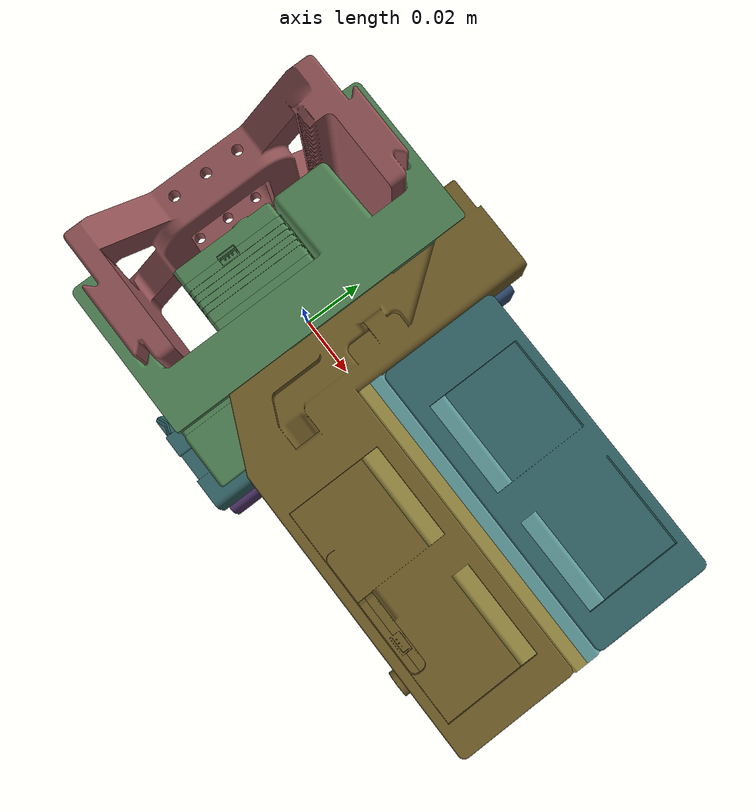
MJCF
<mujoco model="cartesian_hand">
  <compiler angle="radian" meshdir="meshes" autolimits="true" />
  <option timestep="0.0005" iterations="100" integrator="implicitfast" />
  <default>
    <default class="visual">
      <geom type="mesh" contype="0" conaffinity="0" group="2" />
    </default>
    <default class="collision">
      <geom contype="1" conaffinity="0" group="3" condim="3" friction="1.0 0.005 0.0001" solref="0.005 1" />
    </default>
  </default>
  <asset>
    <mesh name="base_visual_steel_mesh" file="base__steel.obj" scale="0.001 0.001 0.001" />
    <mesh name="base_visual_nylon_mesh" file="base__nylon.obj" scale="0.001 0.001 0.001" />
    <mesh name="base_visual_red_mesh" file="base__red.obj" scale="0.001 0.001 0.001" />
    <mesh name="base_col_00_mesh" file="collision_pieces/base_00.obj" scale="0.001 0.001 0.001" />
    <mesh name="base_col_01_mesh" file="collision_pieces/base_01.obj" scale="0.001 0.001 0.001" />
    <mesh name="base_col_02_mesh" file="collision_pieces/base_02.obj" scale="0.001 0.001 0.001" />
    <mesh name="base_col_03_mesh" file="collision_pieces/base_03.obj" scale="0.001 0.001 0.001" />
    <mesh name="base_col_04_mesh" file="collision_pieces/base_04.obj" scale="0.001 0.001 0.001" />
    <mesh name="base_col_05_mesh" file="collision_pieces/base_05.obj" scale="0.001 0.001 0.001" />
    <mesh name="base_col_06_mesh" file="collision_pieces/base_06.obj" scale="0.001 0.001 0.001" />
    <mesh name="base_col_07_mesh" file="collision_pieces/base_07.obj" scale="0.001 0.001 0.001" />
    <mesh name="base_col_08_mesh" file="collision_pieces/base_08.obj" scale="0.001 0.001 0.001" />
    <mesh name="base_col_09_mesh" file="collision_pieces/base_09.obj" scale="0.001 0.001 0.001" />
    <mesh name="base_col_10_mesh" file="collision_pieces/base_10.obj" scale="0.001 0.001 0.001" />
    <mesh name="base_col_11_mesh" file="collision_pieces/base_11.obj" scale="0.001 0.001 0.001" />
    <mesh name="base_col_12_mesh" file="collision_pieces/base_12.obj" scale="0.001 0.001 0.001" />
    <mesh name="base_col_13_mesh" file="collision_pieces/base_13.obj" scale="0.001 0.001 0.001" />
    <mesh name="base_col_14_mesh" file="collision_pieces/base_14.obj" scale="0.001 0.001 0.001" />
    <mesh name="base_col_15_mesh" file="collision_pieces/base_15.obj" scale="0.001 0.001 0.001" />
    <mesh name="base_col_16_mesh" file="collision_pieces/base_16.obj" scale="0.001 0.001 0.001" />
    <mesh name="base_col_17_mesh" file="collision_pieces/base_17.obj" scale="0.001 0.001 0.001" />
    <mesh name="base_col_18_mesh" file="collision_pieces/base_18.obj" scale="0.001 0.001 0.001" />
    <mesh name="base_col_19_mesh" file="collision_pieces/base_19.obj" scale="0.001 0.001 0.001" />
    <mesh name="base_col_20_mesh" file="collision_pieces/base_20.obj" scale="0.001 0.001 0.001" />
    <mesh name="base_col_21_mesh" file="collision_pieces/base_21.obj" scale="0.001 0.001 0.001" />
    <mesh name="base_col_22_mesh" file="collision_pieces/base_22.obj" scale="0.001 0.001 0.001" />
    <mesh name="base_col_23_mesh" file="collision_pieces/base_23.obj" scale="0.001 0.001 0.001" />
    <mesh name="base_col_24_mesh" file="collision_pieces/base_24.obj" scale="0.001 0.001 0.001" />
    <mesh name="base_col_25_mesh" file="collision_pieces/base_25.obj" scale="0.001 0.001 0.001" />
    <mesh name="base_col_26_mesh" file="collision_pieces/base_26.obj" scale="0.001 0.001 0.001" />
    <mesh name="base_col_27_mesh" file="collision_pieces/base_27.obj" scale="0.001 0.001 0.001" />
    <mesh name="base_col_28_mesh" file="collision_pieces/base_28.obj" scale="0.001 0.001 0.001" />
    <mesh name="base_col_29_mesh" file="collision_pieces/base_29.obj" scale="0.001 0.001 0.001" />
    <mesh name="base_col_30_mesh" file="collision_pieces/base_30.obj" scale="0.001 0.001 0.001" />
    <mesh name="base_col_31_mesh" file="collision_pieces/base_31.obj" scale="0.001 0.001 0.001" />
    <mesh name="base_col_32_mesh" file="collision_pieces/base_32.obj" scale="0.001 0.001 0.001" />
    <mesh name="base_col_33_mesh" file="collision_pieces/base_33.obj" scale="0.001 0.001 0.001" />
    <mesh name="base_col_34_mesh" file="collision_pieces/base_34.obj" scale="0.001 0.001 0.001" />
    <mesh name="base_col_35_mesh" file="collision_pieces/base_35.obj" scale="0.001 0.001 0.001" />
    <mesh name="base_col_36_mesh" file="collision_pieces/base_36.obj" scale="0.001 0.001 0.001" />
    <mesh name="base_col_37_mesh" file="collision_pieces/base_37.obj" scale="0.001 0.001 0.001" />
    <mesh name="base_col_38_mesh" file="collision_pieces/base_38.obj" scale="0.001 0.001 0.001" />
    <mesh name="base_col_39_mesh" file="collision_pieces/base_39.obj" scale="0.001 0.001 0.001" />
    <mesh name="base_col_40_mesh" file="collision_pieces/base_40.obj" scale="0.001 0.001 0.001" />
    <mesh name="base_col_41_mesh" file="collision_pieces/base_41.obj" scale="0.001 0.001 0.001" />
    <mesh name="base_col_42_mesh" file="collision_pieces/base_42.obj" scale="0.001 0.001 0.001" />
    <mesh name="base_col_43_mesh" file="collision_pieces/base_43.obj" scale="0.001 0.001 0.001" />
    <mesh name="base_col_44_mesh" file="collision_pieces/base_44.obj" scale="0.001 0.001 0.001" />
    <mesh name="base_col_45_mesh" file="collision_pieces/base_45.obj" scale="0.001 0.001 0.001" />
    <mesh name="base_col_46_mesh" file="collision_pieces/base_46.obj" scale="0.001 0.001 0.001" />
    <mesh name="base_col_47_mesh" file="collision_pieces/base_47.obj" scale="0.001 0.001 0.001" />
    <mesh name="base_col_48_mesh" file="collision_pieces/base_48.obj" scale="0.001 0.001 0.001" />
    <mesh name="base_col_49_mesh" file="collision_pieces/base_49.obj" scale="0.001 0.001 0.001" />
    <mesh name="base_col_50_mesh" file="collision_pieces/base_50.obj" scale="0.001 0.001 0.001" />
    <mesh name="base_col_51_mesh" file="collision_pieces/base_51.obj" scale="0.001 0.001 0.001" />
    <mesh name="base_col_52_mesh" file="collision_pieces/base_52.obj" scale="0.001 0.001 0.001" />
    <mesh name="base_col_53_mesh" file="collision_pieces/base_53.obj" scale="0.001 0.001 0.001" />
    <mesh name="base_col_54_mesh" file="collision_pieces/base_54.obj" scale="0.001 0.001 0.001" />
    <mesh name="base_col_55_mesh" file="collision_pieces/base_55.obj" scale="0.001 0.001 0.001" />
    <mesh name="base_col_56_mesh" file="collision_pieces/base_56.obj" scale="0.001 0.001 0.001" />
    <mesh name="base_col_57_mesh" file="collision_pieces/base_57.obj" scale="0.001 0.001 0.001" />
    <mesh name="base_col_58_mesh" file="collision_pieces/base_58.obj" scale="0.001 0.001 0.001" />
    <mesh name="base_col_59_mesh" file="collision_pieces/base_59.obj" scale="0.001 0.001 0.001" />
    <mesh name="base_col_60_mesh" file="collision_pieces/base_60.obj" scale="0.001 0.001 0.001" />
    <mesh name="base_col_61_mesh" file="collision_pieces/base_61.obj" scale="0.001 0.001 0.001" />
    <mesh name="base_col_62_mesh" file="collision_pieces/base_62.obj" scale="0.001 0.001 0.001" />
    <mesh name="base_col_63_mesh" file="collision_pieces/base_63.obj" scale="0.001 0.001 0.001" />
    <mesh name="base_col_64_mesh" file="collision_pieces/base_64.obj" scale="0.001 0.001 0.001" />
    <mesh name="base_col_65_mesh" file="collision_pieces/base_65.obj" scale="0.001 0.001 0.001" />
    <mesh name="base_col_66_mesh" file="collision_pieces/base_66.obj" scale="0.001 0.001 0.001" />
    <mesh name="base_col_67_mesh" file="collision_pieces/base_67.obj" scale="0.001 0.001 0.001" />
    <mesh name="base_col_68_mesh" file="collision_pieces/base_68.obj" scale="0.001 0.001 0.001" />
    <mesh name="base_col_69_mesh" file="collision_pieces/base_69.obj" scale="0.001 0.001 0.001" />
    <mesh name="base_col_70_mesh" file="collision_pieces/base_70.obj" scale="0.001 0.001 0.001" />
    <mesh name="base_col_71_mesh" file="collision_pieces/base_71.obj" scale="0.001 0.001 0.001" />
    <mesh name="base_col_72_mesh" file="collision_pieces/base_72.obj" scale="0.001 0.001 0.001" />
    <mesh name="base_col_73_mesh" file="collision_pieces/base_73.obj" scale="0.001 0.001 0.001" />
    <mesh name="base_col_74_mesh" file="collision_pieces/base_74.obj" scale="0.001 0.001 0.001" />
    <mesh name="base_col_75_mesh" file="collision_pieces/base_75.obj" scale="0.001 0.001 0.001" />
    <mesh name="base_col_76_mesh" file="collision_pieces/base_76.obj" scale="0.001 0.001 0.001" />
    <mesh name="base_col_77_mesh" file="collision_pieces/base_77.obj" scale="0.001 0.001 0.001" />
    <mesh name="base_col_78_mesh" file="collision_pieces/base_78.obj" scale="0.001 0.001 0.001" />
    <mesh name="base_col_79_mesh" file="collision_pieces/base_79.obj" scale="0.001 0.001 0.001" />
    <mesh name="base_col_80_mesh" file="collision_pieces/base_80.obj" scale="0.001 0.001 0.001" />
    <mesh name="base_col_81_mesh" file="collision_pieces/base_81.obj" scale="0.001 0.001 0.001" />
    <mesh name="base_col_82_mesh" file="collision_pieces/base_82.obj" scale="0.001 0.001 0.001" />
    <mesh name="base_col_83_mesh" file="collision_pieces/base_83.obj" scale="0.001 0.001 0.001" />
    <mesh name="base_col_84_mesh" file="collision_pieces/base_84.obj" scale="0.001 0.001 0.001" />
    <mesh name="base_col_85_mesh" file="collision_pieces/base_85.obj" scale="0.001 0.001 0.001" />
    <mesh name="base_col_86_mesh" file="collision_pieces/base_86.obj" scale="0.001 0.001 0.001" />
    <mesh name="base_col_87_mesh" file="collision_pieces/base_87.obj" scale="0.001 0.001 0.001" />
    <mesh name="base_col_88_mesh" file="collision_pieces/base_88.obj" scale="0.001 0.001 0.001" />
    <mesh name="base_col_89_mesh" file="collision_pieces/base_89.obj" scale="0.001 0.001 0.001" />
    <mesh name="bridge_visual_steel_mesh" file="bridge__steel.obj" scale="0.001 0.001 0.001" />
    <mesh name="bridge_visual_nylon_mesh" file="bridge__nylon.obj" scale="0.001 0.001 0.001" />
    <mesh name="bridge_visual_red_mesh" file="bridge__red.obj" scale="0.001 0.001 0.001" />
    <mesh name="bridge_col_00_mesh" file="collision_pieces/bridge_00.obj" scale="0.001 0.001 0.001" />
    <mesh name="bridge_col_01_mesh" file="collision_pieces/bridge_01.obj" scale="0.001 0.001 0.001" />
    <mesh name="bridge_col_02_mesh" file="collision_pieces/bridge_02.obj" scale="0.001 0.001 0.001" />
    <mesh name="bridge_col_03_mesh" file="collision_pieces/bridge_03.obj" scale="0.001 0.001 0.001" />
    <mesh name="bridge_col_04_mesh" file="collision_pieces/bridge_04.obj" scale="0.001 0.001 0.001" />
    <mesh name="bridge_col_05_mesh" file="collision_pieces/bridge_05.obj" scale="0.001 0.001 0.001" />
    <mesh name="bridge_col_06_mesh" file="collision_pieces/bridge_06.obj" scale="0.001 0.001 0.001" />
    <mesh name="bridge_col_07_mesh" file="collision_pieces/bridge_07.obj" scale="0.001 0.001 0.001" />
    <mesh name="bridge_col_08_mesh" file="collision_pieces/bridge_08.obj" scale="0.001 0.001 0.001" />
    <mesh name="bridge_col_09_mesh" file="collision_pieces/bridge_09.obj" scale="0.001 0.001 0.001" />
    <mesh name="bridge_col_10_mesh" file="collision_pieces/bridge_10.obj" scale="0.001 0.001 0.001" />
    <mesh name="bridge_col_11_mesh" file="collision_pieces/bridge_11.obj" scale="0.001 0.001 0.001" />
    <mesh name="bridge_col_12_mesh" file="collision_pieces/bridge_12.obj" scale="0.001 0.001 0.001" />
    <mesh name="bridge_col_13_mesh" file="collision_pieces/bridge_13.obj" scale="0.001 0.001 0.001" />
    <mesh name="bridge_col_14_mesh" file="collision_pieces/bridge_14.obj" scale="0.001 0.001 0.001" />
    <mesh name="bridge_col_15_mesh" file="collision_pieces/bridge_15.obj" scale="0.001 0.001 0.001" />
    <mesh name="bridge_col_16_mesh" file="collision_pieces/bridge_16.obj" scale="0.001 0.001 0.001" />
    <mesh name="bridge_col_17_mesh" file="collision_pieces/bridge_17.obj" scale="0.001 0.001 0.001" />
    <mesh name="bridge_col_18_mesh" file="collision_pieces/bridge_18.obj" scale="0.001 0.001 0.001" />
    <mesh name="bridge_col_19_mesh" file="collision_pieces/bridge_19.obj" scale="0.001 0.001 0.001" />
    <mesh name="bridge_col_20_mesh" file="collision_pieces/bridge_20.obj" scale="0.001 0.001 0.001" />
    <mesh name="bridge_col_21_mesh" file="collision_pieces/bridge_21.obj" scale="0.001 0.001 0.001" />
    <mesh name="bridge_col_22_mesh" file="collision_pieces/bridge_22.obj" scale="0.001 0.001 0.001" />
    <mesh name="bridge_col_23_mesh" file="collision_pieces/bridge_23.obj" scale="0.001 0.001 0.001" />
    <mesh name="bridge_col_24_mesh" file="collision_pieces/bridge_24.obj" scale="0.001 0.001 0.001" />
    <mesh name="bridge_col_25_mesh" file="collision_pieces/bridge_25.obj" scale="0.001 0.001 0.001" />
    <mesh name="bridge_col_26_mesh" file="collision_pieces/bridge_26.obj" scale="0.001 0.001 0.001" />
    <mesh name="bridge_col_27_mesh" file="collision_pieces/bridge_27.obj" scale="0.001 0.001 0.001" />
    <mesh name="bridge_col_28_mesh" file="collision_pieces/bridge_28.obj" scale="0.001 0.001 0.001" />
    <mesh name="bridge_col_29_mesh" file="collision_pieces/bridge_29.obj" scale="0.001 0.001 0.001" />
    <mesh name="bridge_col_30_mesh" file="collision_pieces/bridge_30.obj" scale="0.001 0.001 0.001" />
    <mesh name="bridge_col_31_mesh" file="collision_pieces/bridge_31.obj" scale="0.001 0.001 0.001" />
    <mesh name="bridge_col_32_mesh" file="collision_pieces/bridge_32.obj" scale="0.001 0.001 0.001" />
    <mesh name="bridge_col_33_mesh" file="collision_pieces/bridge_33.obj" scale="0.001 0.001 0.001" />
    <mesh name="bridge_col_34_mesh" file="collision_pieces/bridge_34.obj" scale="0.001 0.001 0.001" />
    <mesh name="bridge_col_35_mesh" file="collision_pieces/bridge_35.obj" scale="0.001 0.001 0.001" />
    <mesh name="bridge_col_36_mesh" file="collision_pieces/bridge_36.obj" scale="0.001 0.001 0.001" />
    <mesh name="bridge_col_37_mesh" file="collision_pieces/bridge_37.obj" scale="0.001 0.001 0.001" />
    <mesh name="bridge_col_38_mesh" file="collision_pieces/bridge_38.obj" scale="0.001 0.001 0.001" />
    <mesh name="bridge_col_39_mesh" file="collision_pieces/bridge_39.obj" scale="0.001 0.001 0.001" />
    <mesh name="bridge_col_40_mesh" file="collision_pieces/bridge_40.obj" scale="0.001 0.001 0.001" />
    <mesh name="bridge_col_41_mesh" file="collision_pieces/bridge_41.obj" scale="0.001 0.001 0.001" />
    <mesh name="bridge_col_42_mesh" file="collision_pieces/bridge_42.obj" scale="0.001 0.001 0.001" />
    <mesh name="bridge_col_43_mesh" file="collision_pieces/bridge_43.obj" scale="0.001 0.001 0.001" />
    <mesh name="bridge_col_44_mesh" file="collision_pieces/bridge_44.obj" scale="0.001 0.001 0.001" />
    <mesh name="bridge_col_45_mesh" file="collision_pieces/bridge_45.obj" scale="0.001 0.001 0.001" />
    <mesh name="bridge_col_46_mesh" file="collision_pieces/bridge_46.obj" scale="0.001 0.001 0.001" />
    <mesh name="bridge_col_47_mesh" file="collision_pieces/bridge_47.obj" scale="0.001 0.001 0.001" />
    <mesh name="bridge_col_48_mesh" file="collision_pieces/bridge_48.obj" scale="0.001 0.001 0.001" />
    <mesh name="bridge_col_49_mesh" file="collision_pieces/bridge_49.obj" scale="0.001 0.001 0.001" />
    <mesh name="bridge_col_50_mesh" file="collision_pieces/bridge_50.obj" scale="0.001 0.001 0.001" />
    <mesh name="bridge_col_51_mesh" file="collision_pieces/bridge_51.obj" scale="0.001 0.001 0.001" />
    <mesh name="bridge_col_52_mesh" file="collision_pieces/bridge_52.obj" scale="0.001 0.001 0.001" />
    <mesh name="bridge_col_53_mesh" file="collision_pieces/bridge_53.obj" scale="0.001 0.001 0.001" />
    <mesh name="bridge_col_54_mesh" file="collision_pieces/bridge_54.obj" scale="0.001 0.001 0.001" />
    <mesh name="bridge_col_55_mesh" file="collision_pieces/bridge_55.obj" scale="0.001 0.001 0.001" />
    <mesh name="bridge_col_56_mesh" file="collision_pieces/bridge_56.obj" scale="0.001 0.001 0.001" />
    <mesh name="bridge_col_57_mesh" file="collision_pieces/bridge_57.obj" scale="0.001 0.001 0.001" />
    <mesh name="bridge_col_58_mesh" file="collision_pieces/bridge_58.obj" scale="0.001 0.001 0.001" />
    <mesh name="bridge_col_59_mesh" file="collision_pieces/bridge_59.obj" scale="0.001 0.001 0.001" />
    <mesh name="bridge_col_60_mesh" file="collision_pieces/bridge_60.obj" scale="0.001 0.001 0.001" />
    <mesh name="bridge_col_61_mesh" file="collision_pieces/bridge_61.obj" scale="0.001 0.001 0.001" />
    <mesh name="bridge_col_62_mesh" file="collision_pieces/bridge_62.obj" scale="0.001 0.001 0.001" />
    <mesh name="bridge_col_63_mesh" file="collision_pieces/bridge_63.obj" scale="0.001 0.001 0.001" />
    <mesh name="bridge_col_64_mesh" file="collision_pieces/bridge_64.obj" scale="0.001 0.001 0.001" />
    <mesh name="bridge_col_65_mesh" file="collision_pieces/bridge_65.obj" scale="0.001 0.001 0.001" />
    <mesh name="bridge_col_66_mesh" file="collision_pieces/bridge_66.obj" scale="0.001 0.001 0.001" />
    <mesh name="bridge_col_67_mesh" file="collision_pieces/bridge_67.obj" scale="0.001 0.001 0.001" />
    <mesh name="bridge_col_68_mesh" file="collision_pieces/bridge_68.obj" scale="0.001 0.001 0.001" />
    <mesh name="bridge_col_69_mesh" file="collision_pieces/bridge_69.obj" scale="0.001 0.001 0.001" />
    <mesh name="bridge_col_70_mesh" file="collision_pieces/bridge_70.obj" scale="0.001 0.001 0.001" />
    <mesh name="bridge_col_71_mesh" file="collision_pieces/bridge_71.obj" scale="0.001 0.001 0.001" />
    <mesh name="bridge_col_72_mesh" file="collision_pieces/bridge_72.obj" scale="0.001 0.001 0.001" />
    <mesh name="bridge_col_73_mesh" file="collision_pieces/bridge_73.obj" scale="0.001 0.001 0.001" />
    <mesh name="bridge_col_74_mesh" file="collision_pieces/bridge_74.obj" scale="0.001 0.001 0.001" />
    <mesh name="bridge_col_75_mesh" file="collision_pieces/bridge_75.obj" scale="0.001 0.001 0.001" />
    <mesh name="bridge_col_76_mesh" file="collision_pieces/bridge_76.obj" scale="0.001 0.001 0.001" />
    <mesh name="bridge_col_77_mesh" file="collision_pieces/bridge_77.obj" scale="0.001 0.001 0.001" />
    <mesh name="bridge_col_78_mesh" file="collision_pieces/bridge_78.obj" scale="0.001 0.001 0.001" />
    <mesh name="bridge_col_79_mesh" file="collision_pieces/bridge_79.obj" scale="0.001 0.001 0.001" />
    <mesh name="left_up_rack_visual_steel_mesh" file="left_up_rack__steel.obj" scale="0.001 0.001 0.001" />
    <mesh name="left_up_rack_visual_nylon_mesh" file="left_up_rack__nylon.obj" scale="0.001 0.001 0.001" />
    <mesh name="left_up_rack_visual_red_mesh" file="left_up_rack__red.obj" scale="0.001 0.001 0.001" />
    <mesh name="left_up_rack_col_00_mesh" file="collision_pieces/left_up_rack_00.obj" scale="0.001 0.001 0.001" />
    <mesh name="left_up_rack_col_01_mesh" file="collision_pieces/left_up_rack_01.obj" scale="0.001 0.001 0.001" />
    <mesh name="left_up_rack_col_02_mesh" file="collision_pieces/left_up_rack_02.obj" scale="0.001 0.001 0.001" />
    <mesh name="left_up_rack_col_03_mesh" file="collision_pieces/left_up_rack_03.obj" scale="0.001 0.001 0.001" />
    <mesh name="left_up_rack_col_04_mesh" file="collision_pieces/left_up_rack_04.obj" scale="0.001 0.001 0.001" />
    <mesh name="left_up_rack_col_05_mesh" file="collision_pieces/left_up_rack_05.obj" scale="0.001 0.001 0.001" />
    <mesh name="left_up_rack_col_06_mesh" file="collision_pieces/left_up_rack_06.obj" scale="0.001 0.001 0.001" />
    <mesh name="left_up_rack_col_07_mesh" file="collision_pieces/left_up_rack_07.obj" scale="0.001 0.001 0.001" />
    <mesh name="left_up_rack_col_08_mesh" file="collision_pieces/left_up_rack_08.obj" scale="0.001 0.001 0.001" />
    <mesh name="left_up_rack_col_09_mesh" file="collision_pieces/left_up_rack_09.obj" scale="0.001 0.001 0.001" />
    <mesh name="left_up_rack_col_10_mesh" file="collision_pieces/left_up_rack_10.obj" scale="0.001 0.001 0.001" />
    <mesh name="left_up_rack_col_11_mesh" file="collision_pieces/left_up_rack_11.obj" scale="0.001 0.001 0.001" />
    <mesh name="left_up_rack_col_12_mesh" file="collision_pieces/left_up_rack_12.obj" scale="0.001 0.001 0.001" />
    <mesh name="left_up_rack_col_13_mesh" file="collision_pieces/left_up_rack_13.obj" scale="0.001 0.001 0.001" />
    <mesh name="left_up_rack_col_14_mesh" file="collision_pieces/left_up_rack_14.obj" scale="0.001 0.001 0.001" />
    <mesh name="left_up_rack_col_15_mesh" file="collision_pieces/left_up_rack_15.obj" scale="0.001 0.001 0.001" />
    <mesh name="left_up_rack_col_16_mesh" file="collision_pieces/left_up_rack_16.obj" scale="0.001 0.001 0.001" />
    <mesh name="left_up_rack_col_17_mesh" file="collision_pieces/left_up_rack_17.obj" scale="0.001 0.001 0.001" />
    <mesh name="left_up_rack_col_18_mesh" file="collision_pieces/left_up_rack_18.obj" scale="0.001 0.001 0.001" />
    <mesh name="left_up_rack_col_19_mesh" file="collision_pieces/left_up_rack_19.obj" scale="0.001 0.001 0.001" />
    <mesh name="left_up_rack_col_20_mesh" file="collision_pieces/left_up_rack_20.obj" scale="0.001 0.001 0.001" />
    <mesh name="left_up_rack_col_21_mesh" file="collision_pieces/left_up_rack_21.obj" scale="0.001 0.001 0.001" />
    <mesh name="left_up_rack_col_22_mesh" file="collision_pieces/left_up_rack_22.obj" scale="0.001 0.001 0.001" />
    <mesh name="left_up_rack_col_23_mesh" file="collision_pieces/left_up_rack_23.obj" scale="0.001 0.001 0.001" />
    <mesh name="left_up_rack_col_24_mesh" file="collision_pieces/left_up_rack_24.obj" scale="0.001 0.001 0.001" />
    <mesh name="left_up_rack_col_25_mesh" file="collision_pieces/left_up_rack_25.obj" scale="0.001 0.001 0.001" />
    <mesh name="left_up_rack_col_26_mesh" file="collision_pieces/left_up_rack_26.obj" scale="0.001 0.001 0.001" />
    <mesh name="left_up_rack_col_27_mesh" file="collision_pieces/left_up_rack_27.obj" scale="0.001 0.001 0.001" />
    <mesh name="left_up_rack_col_28_mesh" file="collision_pieces/left_up_rack_28.obj" scale="0.001 0.001 0.001" />
    <mesh name="left_up_rack_col_29_mesh" file="collision_pieces/left_up_rack_29.obj" scale="0.001 0.001 0.001" />
    <mesh name="left_up_rack_col_30_mesh" file="collision_pieces/left_up_rack_30.obj" scale="0.001 0.001 0.001" />
    <mesh name="left_up_rack_col_31_mesh" file="collision_pieces/left_up_rack_31.obj" scale="0.001 0.001 0.001" />
    <mesh name="left_up_rack_col_32_mesh" file="collision_pieces/left_up_rack_32.obj" scale="0.001 0.001 0.001" />
    <mesh name="left_up_rack_col_33_mesh" file="collision_pieces/left_up_rack_33.obj" scale="0.001 0.001 0.001" />
    <mesh name="left_up_rack_col_34_mesh" file="collision_pieces/left_up_rack_34.obj" scale="0.001 0.001 0.001" />
    <mesh name="left_up_rack_col_35_mesh" file="collision_pieces/left_up_rack_35.obj" scale="0.001 0.001 0.001" />
    <mesh name="left_up_rack_col_36_mesh" file="collision_pieces/left_up_rack_36.obj" scale="0.001 0.001 0.001" />
    <mesh name="left_up_rack_col_37_mesh" file="collision_pieces/left_up_rack_37.obj" scale="0.001 0.001 0.001" />
    <mesh name="left_up_rack_col_38_mesh" file="collision_pieces/left_up_rack_38.obj" scale="0.001 0.001 0.001" />
    <mesh name="left_up_rack_col_39_mesh" file="collision_pieces/left_up_rack_39.obj" scale="0.001 0.001 0.001" />
    <mesh name="left_up_rack_col_40_mesh" file="collision_pieces/left_up_rack_40.obj" scale="0.001 0.001 0.001" />
    <mesh name="left_up_rack_col_41_mesh" file="collision_pieces/left_up_rack_41.obj" scale="0.001 0.001 0.001" />
    <mesh name="left_up_rack_col_42_mesh" file="collision_pieces/left_up_rack_42.obj" scale="0.001 0.001 0.001" />
    <mesh name="left_up_rack_col_43_mesh" file="collision_pieces/left_up_rack_43.obj" scale="0.001 0.001 0.001" />
    <mesh name="left_up_rack_col_44_mesh" file="collision_pieces/left_up_rack_44.obj" scale="0.001 0.001 0.001" />
    <mesh name="left_up_rack_col_45_mesh" file="collision_pieces/left_up_rack_45.obj" scale="0.001 0.001 0.001" />
    <mesh name="left_up_rack_col_46_mesh" file="collision_pieces/left_up_rack_46.obj" scale="0.001 0.001 0.001" />
    <mesh name="left_up_rack_col_47_mesh" file="collision_pieces/left_up_rack_47.obj" scale="0.001 0.001 0.001" />
    <mesh name="left_up_rack_col_48_mesh" file="collision_pieces/left_up_rack_48.obj" scale="0.001 0.001 0.001" />
    <mesh name="left_up_rack_col_49_mesh" file="collision_pieces/left_up_rack_49.obj" scale="0.001 0.001 0.001" />
    <mesh name="left_up_rack_col_50_mesh" file="collision_pieces/left_up_rack_50.obj" scale="0.001 0.001 0.001" />
    <mesh name="left_up_rack_col_51_mesh" file="collision_pieces/left_up_rack_51.obj" scale="0.001 0.001 0.001" />
    <mesh name="left_up_finger_visual_mesh" file="left_up_finger__nylon.obj" scale="0.001 0.001 0.001" />
    <mesh name="left_up_finger_col_00_mesh" file="collision_pieces/left_up_finger_00.obj" scale="0.001 0.001 0.001" />
    <mesh name="left_up_finger_col_01_mesh" file="collision_pieces/left_up_finger_01.obj" scale="0.001 0.001 0.001" />
    <mesh name="left_up_finger_col_02_mesh" file="collision_pieces/left_up_finger_02.obj" scale="0.001 0.001 0.001" />
    <mesh name="left_up_finger_col_03_mesh" file="collision_pieces/left_up_finger_03.obj" scale="0.001 0.001 0.001" />
    <mesh name="left_up_finger_col_04_mesh" file="collision_pieces/left_up_finger_04.obj" scale="0.001 0.001 0.001" />
    <mesh name="left_up_finger_col_05_mesh" file="collision_pieces/left_up_finger_05.obj" scale="0.001 0.001 0.001" />
    <mesh name="left_up_finger_col_06_mesh" file="collision_pieces/left_up_finger_06.obj" scale="0.001 0.001 0.001" />
    <mesh name="left_up_finger_col_07_mesh" file="collision_pieces/left_up_finger_07.obj" scale="0.001 0.001 0.001" />
    <mesh name="left_up_finger_col_08_mesh" file="collision_pieces/left_up_finger_08.obj" scale="0.001 0.001 0.001" />
    <mesh name="left_up_finger_col_09_mesh" file="collision_pieces/left_up_finger_09.obj" scale="0.001 0.001 0.001" />
    <mesh name="left_up_finger_col_10_mesh" file="collision_pieces/left_up_finger_10.obj" scale="0.001 0.001 0.001" />
    <mesh name="left_up_finger_col_11_mesh" file="collision_pieces/left_up_finger_11.obj" scale="0.001 0.001 0.001" />
    <mesh name="left_up_finger_col_12_mesh" file="collision_pieces/left_up_finger_12.obj" scale="0.001 0.001 0.001" />
    <mesh name="left_up_finger_col_13_mesh" file="collision_pieces/left_up_finger_13.obj" scale="0.001 0.001 0.001" />
    <mesh name="left_up_finger_col_14_mesh" file="collision_pieces/left_up_finger_14.obj" scale="0.001 0.001 0.001" />
    <mesh name="left_up_finger_col_15_mesh" file="collision_pieces/left_up_finger_15.obj" scale="0.001 0.001 0.001" />
    <mesh name="left_up_finger_col_16_mesh" file="collision_pieces/left_up_finger_16.obj" scale="0.001 0.001 0.001" />
    <mesh name="left_up_finger_col_17_mesh" file="collision_pieces/left_up_finger_17.obj" scale="0.001 0.001 0.001" />
    <mesh name="left_up_finger_col_18_mesh" file="collision_pieces/left_up_finger_18.obj" scale="0.001 0.001 0.001" />
    <mesh name="left_up_finger_col_19_mesh" file="collision_pieces/left_up_finger_19.obj" scale="0.001 0.001 0.001" />
    <mesh name="left_up_finger_col_20_mesh" file="collision_pieces/left_up_finger_20.obj" scale="0.001 0.001 0.001" />
    <mesh name="left_up_finger_col_21_mesh" file="collision_pieces/left_up_finger_21.obj" scale="0.001 0.001 0.001" />
    <mesh name="left_up_finger_col_22_mesh" file="collision_pieces/left_up_finger_22.obj" scale="0.001 0.001 0.001" />
    <mesh name="left_up_finger_col_23_mesh" file="collision_pieces/left_up_finger_23.obj" scale="0.001 0.001 0.001" />
    <mesh name="left_up_finger_col_24_mesh" file="collision_pieces/left_up_finger_24.obj" scale="0.001 0.001 0.001" />
    <mesh name="left_up_finger_col_25_mesh" file="collision_pieces/left_up_finger_25.obj" scale="0.001 0.001 0.001" />
    <mesh name="left_up_finger_col_26_mesh" file="collision_pieces/left_up_finger_26.obj" scale="0.001 0.001 0.001" />
    <mesh name="left_up_finger_col_27_mesh" file="collision_pieces/left_up_finger_27.obj" scale="0.001 0.001 0.001" />
    <mesh name="left_up_finger_col_28_mesh" file="collision_pieces/left_up_finger_28.obj" scale="0.001 0.001 0.001" />
    <mesh name="left_up_finger_col_29_mesh" file="collision_pieces/left_up_finger_29.obj" scale="0.001 0.001 0.001" />
    <mesh name="right_up_rack_visual_steel_mesh" file="right_up_rack__steel.obj" scale="0.001 0.001 0.001" />
    <mesh name="right_up_rack_visual_nylon_mesh" file="right_up_rack__nylon.obj" scale="0.001 0.001 0.001" />
    <mesh name="right_up_rack_visual_red_mesh" file="right_up_rack__red.obj" scale="0.001 0.001 0.001" />
    <mesh name="right_up_rack_col_00_mesh" file="collision_pieces/right_up_rack_00.obj" scale="0.001 0.001 0.001" />
    <mesh name="right_up_rack_col_01_mesh" file="collision_pieces/right_up_rack_01.obj" scale="0.001 0.001 0.001" />
    <mesh name="right_up_rack_col_02_mesh" file="collision_pieces/right_up_rack_02.obj" scale="0.001 0.001 0.001" />
    <mesh name="right_up_rack_col_03_mesh" file="collision_pieces/right_up_rack_03.obj" scale="0.001 0.001 0.001" />
    <mesh name="right_up_rack_col_04_mesh" file="collision_pieces/right_up_rack_04.obj" scale="0.001 0.001 0.001" />
    <mesh name="right_up_rack_col_05_mesh" file="collision_pieces/right_up_rack_05.obj" scale="0.001 0.001 0.001" />
    <mesh name="right_up_rack_col_06_mesh" file="collision_pieces/right_up_rack_06.obj" scale="0.001 0.001 0.001" />
    <mesh name="right_up_rack_col_07_mesh" file="collision_pieces/right_up_rack_07.obj" scale="0.001 0.001 0.001" />
    <mesh name="right_up_rack_col_08_mesh" file="collision_pieces/right_up_rack_08.obj" scale="0.001 0.001 0.001" />
    <mesh name="right_up_rack_col_09_mesh" file="collision_pieces/right_up_rack_09.obj" scale="0.001 0.001 0.001" />
    <mesh name="right_up_rack_col_10_mesh" file="collision_pieces/right_up_rack_10.obj" scale="0.001 0.001 0.001" />
    <mesh name="right_up_rack_col_11_mesh" file="collision_pieces/right_up_rack_11.obj" scale="0.001 0.001 0.001" />
    <mesh name="right_up_rack_col_12_mesh" file="collision_pieces/right_up_rack_12.obj" scale="0.001 0.001 0.001" />
    <mesh name="right_up_rack_col_13_mesh" file="collision_pieces/right_up_rack_13.obj" scale="0.001 0.001 0.001" />
    <mesh name="right_up_rack_col_14_mesh" file="collision_pieces/right_up_rack_14.obj" scale="0.001 0.001 0.001" />
    <mesh name="right_up_rack_col_15_mesh" file="collision_pieces/right_up_rack_15.obj" scale="0.001 0.001 0.001" />
    <mesh name="right_up_rack_col_16_mesh" file="collision_pieces/right_up_rack_16.obj" scale="0.001 0.001 0.001" />
    <mesh name="right_up_rack_col_17_mesh" file="collision_pieces/right_up_rack_17.obj" scale="0.001 0.001 0.001" />
    <mesh name="right_up_rack_col_18_mesh" file="collision_pieces/right_up_rack_18.obj" scale="0.001 0.001 0.001" />
    <mesh name="right_up_rack_col_19_mesh" file="collision_pieces/right_up_rack_19.obj" scale="0.001 0.001 0.001" />
    <mesh name="right_up_rack_col_20_mesh" file="collision_pieces/right_up_rack_20.obj" scale="0.001 0.001 0.001" />
    <mesh name="right_up_rack_col_21_mesh" file="collision_pieces/right_up_rack_21.obj" scale="0.001 0.001 0.001" />
    <mesh name="right_up_rack_col_22_mesh" file="collision_pieces/right_up_rack_22.obj" scale="0.001 0.001 0.001" />
    <mesh name="right_up_rack_col_23_mesh" file="collision_pieces/right_up_rack_23.obj" scale="0.001 0.001 0.001" />
    <mesh name="right_up_rack_col_24_mesh" file="collision_pieces/right_up_rack_24.obj" scale="0.001 0.001 0.001" />
    <mesh name="right_up_rack_col_25_mesh" file="collision_pieces/right_up_rack_25.obj" scale="0.001 0.001 0.001" />
    <mesh name="right_up_rack_col_26_mesh" file="collision_pieces/right_up_rack_26.obj" scale="0.001 0.001 0.001" />
    <mesh name="right_up_rack_col_27_mesh" file="collision_pieces/right_up_rack_27.obj" scale="0.001 0.001 0.001" />
    <mesh name="right_up_rack_col_28_mesh" file="collision_pieces/right_up_rack_28.obj" scale="0.001 0.001 0.001" />
    <mesh name="right_up_rack_col_29_mesh" file="collision_pieces/right_up_rack_29.obj" scale="0.001 0.001 0.001" />
    <mesh name="right_up_rack_col_30_mesh" file="collision_pieces/right_up_rack_30.obj" scale="0.001 0.001 0.001" />
    <mesh name="right_up_rack_col_31_mesh" file="collision_pieces/right_up_rack_31.obj" scale="0.001 0.001 0.001" />
    <mesh name="right_up_rack_col_32_mesh" file="collision_pieces/right_up_rack_32.obj" scale="0.001 0.001 0.001" />
    <mesh name="right_up_rack_col_33_mesh" file="collision_pieces/right_up_rack_33.obj" scale="0.001 0.001 0.001" />
    <mesh name="right_up_rack_col_34_mesh" file="collision_pieces/right_up_rack_34.obj" scale="0.001 0.001 0.001" />
    <mesh name="right_up_rack_col_35_mesh" file="collision_pieces/right_up_rack_35.obj" scale="0.001 0.001 0.001" />
    <mesh name="right_up_rack_col_36_mesh" file="collision_pieces/right_up_rack_36.obj" scale="0.001 0.001 0.001" />
    <mesh name="right_up_rack_col_37_mesh" file="collision_pieces/right_up_rack_37.obj" scale="0.001 0.001 0.001" />
    <mesh name="right_up_rack_col_38_mesh" file="collision_pieces/right_up_rack_38.obj" scale="0.001 0.001 0.001" />
    <mesh name="right_up_rack_col_39_mesh" file="collision_pieces/right_up_rack_39.obj" scale="0.001 0.001 0.001" />
    <mesh name="right_up_rack_col_40_mesh" file="collision_pieces/right_up_rack_40.obj" scale="0.001 0.001 0.001" />
    <mesh name="right_up_rack_col_41_mesh" file="collision_pieces/right_up_rack_41.obj" scale="0.001 0.001 0.001" />
    <mesh name="right_up_rack_col_42_mesh" file="collision_pieces/right_up_rack_42.obj" scale="0.001 0.001 0.001" />
    <mesh name="right_up_rack_col_43_mesh" file="collision_pieces/right_up_rack_43.obj" scale="0.001 0.001 0.001" />
    <mesh name="right_up_rack_col_44_mesh" file="collision_pieces/right_up_rack_44.obj" scale="0.001 0.001 0.001" />
    <mesh name="right_up_rack_col_45_mesh" file="collision_pieces/right_up_rack_45.obj" scale="0.001 0.001 0.001" />
    <mesh name="right_up_rack_col_46_mesh" file="collision_pieces/right_up_rack_46.obj" scale="0.001 0.001 0.001" />
    <mesh name="right_up_rack_col_47_mesh" file="collision_pieces/right_up_rack_47.obj" scale="0.001 0.001 0.001" />
    <mesh name="right_up_rack_col_48_mesh" file="collision_pieces/right_up_rack_48.obj" scale="0.001 0.001 0.001" />
    <mesh name="right_up_rack_col_49_mesh" file="collision_pieces/right_up_rack_49.obj" scale="0.001 0.001 0.001" />
    <mesh name="right_up_rack_col_50_mesh" file="collision_pieces/right_up_rack_50.obj" scale="0.001 0.001 0.001" />
    <mesh name="right_up_rack_col_51_mesh" file="collision_pieces/right_up_rack_51.obj" scale="0.001 0.001 0.001" />
    <mesh name="right_up_finger_visual_mesh" file="right_up_finger__nylon.obj" scale="0.001 0.001 0.001" />
    <mesh name="right_up_finger_col_00_mesh" file="collision_pieces/right_up_finger_00.obj" scale="0.001 0.001 0.001" />
    <mesh name="right_up_finger_col_01_mesh" file="collision_pieces/right_up_finger_01.obj" scale="0.001 0.001 0.001" />
    <mesh name="right_up_finger_col_02_mesh" file="collision_pieces/right_up_finger_02.obj" scale="0.001 0.001 0.001" />
    <mesh name="right_up_finger_col_03_mesh" file="collision_pieces/right_up_finger_03.obj" scale="0.001 0.001 0.001" />
    <mesh name="right_up_finger_col_04_mesh" file="collision_pieces/right_up_finger_04.obj" scale="0.001 0.001 0.001" />
    <mesh name="right_up_finger_col_05_mesh" file="collision_pieces/right_up_finger_05.obj" scale="0.001 0.001 0.001" />
    <mesh name="right_up_finger_col_06_mesh" file="collision_pieces/right_up_finger_06.obj" scale="0.001 0.001 0.001" />
    <mesh name="right_up_finger_col_07_mesh" file="collision_pieces/right_up_finger_07.obj" scale="0.001 0.001 0.001" />
    <mesh name="right_up_finger_col_08_mesh" file="collision_pieces/right_up_finger_08.obj" scale="0.001 0.001 0.001" />
    <mesh name="right_up_finger_col_09_mesh" file="collision_pieces/right_up_finger_09.obj" scale="0.001 0.001 0.001" />
    <mesh name="right_up_finger_col_10_mesh" file="collision_pieces/right_up_finger_10.obj" scale="0.001 0.001 0.001" />
    <mesh name="right_up_finger_col_11_mesh" file="collision_pieces/right_up_finger_11.obj" scale="0.001 0.001 0.001" />
    <mesh name="right_up_finger_col_12_mesh" file="collision_pieces/right_up_finger_12.obj" scale="0.001 0.001 0.001" />
    <mesh name="right_up_finger_col_13_mesh" file="collision_pieces/right_up_finger_13.obj" scale="0.001 0.001 0.001" />
    <mesh name="right_up_finger_col_14_mesh" file="collision_pieces/right_up_finger_14.obj" scale="0.001 0.001 0.001" />
    <mesh name="right_up_finger_col_15_mesh" file="collision_pieces/right_up_finger_15.obj" scale="0.001 0.001 0.001" />
    <mesh name="right_up_finger_col_16_mesh" file="collision_pieces/right_up_finger_16.obj" scale="0.001 0.001 0.001" />
    <mesh name="right_up_finger_col_17_mesh" file="collision_pieces/right_up_finger_17.obj" scale="0.001 0.001 0.001" />
    <mesh name="right_up_finger_col_18_mesh" file="collision_pieces/right_up_finger_18.obj" scale="0.001 0.001 0.001" />
    <mesh name="right_up_finger_col_19_mesh" file="collision_pieces/right_up_finger_19.obj" scale="0.001 0.001 0.001" />
    <mesh name="left_down_rack_visual_steel_mesh" file="left_down_rack__steel.obj" scale="0.001 0.001 0.001" />
    <mesh name="left_down_rack_visual_nylon_mesh" file="left_down_rack__nylon.obj" scale="0.001 0.001 0.001" />
    <mesh name="left_down_rack_visual_red_mesh" file="left_down_rack__red.obj" scale="0.001 0.001 0.001" />
    <mesh name="left_down_rack_col_00_mesh" file="collision_pieces/left_down_rack_00.obj" scale="0.001 0.001 0.001" />
    <mesh name="left_down_rack_col_01_mesh" file="collision_pieces/left_down_rack_01.obj" scale="0.001 0.001 0.001" />
    <mesh name="left_down_rack_col_02_mesh" file="collision_pieces/left_down_rack_02.obj" scale="0.001 0.001 0.001" />
    <mesh name="left_down_rack_col_03_mesh" file="collision_pieces/left_down_rack_03.obj" scale="0.001 0.001 0.001" />
    <mesh name="left_down_rack_col_04_mesh" file="collision_pieces/left_down_rack_04.obj" scale="0.001 0.001 0.001" />
    <mesh name="left_down_rack_col_05_mesh" file="collision_pieces/left_down_rack_05.obj" scale="0.001 0.001 0.001" />
    <mesh name="left_down_rack_col_06_mesh" file="collision_pieces/left_down_rack_06.obj" scale="0.001 0.001 0.001" />
    <mesh name="left_down_rack_col_07_mesh" file="collision_pieces/left_down_rack_07.obj" scale="0.001 0.001 0.001" />
    <mesh name="left_down_rack_col_08_mesh" file="collision_pieces/left_down_rack_08.obj" scale="0.001 0.001 0.001" />
    <mesh name="left_down_rack_col_09_mesh" file="collision_pieces/left_down_rack_09.obj" scale="0.001 0.001 0.001" />
    <mesh name="left_down_rack_col_10_mesh" file="collision_pieces/left_down_rack_10.obj" scale="0.001 0.001 0.001" />
    <mesh name="left_down_rack_col_11_mesh" file="collision_pieces/left_down_rack_11.obj" scale="0.001 0.001 0.001" />
    <mesh name="left_down_rack_col_12_mesh" file="collision_pieces/left_down_rack_12.obj" scale="0.001 0.001 0.001" />
    <mesh name="left_down_rack_col_13_mesh" file="collision_pieces/left_down_rack_13.obj" scale="0.001 0.001 0.001" />
    <mesh name="left_down_rack_col_14_mesh" file="collision_pieces/left_down_rack_14.obj" scale="0.001 0.001 0.001" />
    <mesh name="left_down_rack_col_15_mesh" file="collision_pieces/left_down_rack_15.obj" scale="0.001 0.001 0.001" />
    <mesh name="left_down_rack_col_16_mesh" file="collision_pieces/left_down_rack_16.obj" scale="0.001 0.001 0.001" />
    <mesh name="left_down_rack_col_17_mesh" file="collision_pieces/left_down_rack_17.obj" scale="0.001 0.001 0.001" />
    <mesh name="left_down_rack_col_18_mesh" file="collision_pieces/left_down_rack_18.obj" scale="0.001 0.001 0.001" />
    <mesh name="left_down_rack_col_19_mesh" file="collision_pieces/left_down_rack_19.obj" scale="0.001 0.001 0.001" />
    <mesh name="left_down_rack_col_20_mesh" file="collision_pieces/left_down_rack_20.obj" scale="0.001 0.001 0.001" />
    <mesh name="left_down_rack_col_21_mesh" file="collision_pieces/left_down_rack_21.obj" scale="0.001 0.001 0.001" />
    <mesh name="left_down_rack_col_22_mesh" file="collision_pieces/left_down_rack_22.obj" scale="0.001 0.001 0.001" />
    <mesh name="left_down_rack_col_23_mesh" file="collision_pieces/left_down_rack_23.obj" scale="0.001 0.001 0.001" />
    <mesh name="left_down_rack_col_24_mesh" file="collision_pieces/left_down_rack_24.obj" scale="0.001 0.001 0.001" />
    <mesh name="left_down_rack_col_25_mesh" file="collision_pieces/left_down_rack_25.obj" scale="0.001 0.001 0.001" />
    <mesh name="left_down_rack_col_26_mesh" file="collision_pieces/left_down_rack_26.obj" scale="0.001 0.001 0.001" />
    <mesh name="left_down_rack_col_27_mesh" file="collision_pieces/left_down_rack_27.obj" scale="0.001 0.001 0.001" />
    <mesh name="left_down_rack_col_28_mesh" file="collision_pieces/left_down_rack_28.obj" scale="0.001 0.001 0.001" />
    <mesh name="left_down_rack_col_29_mesh" file="collision_pieces/left_down_rack_29.obj" scale="0.001 0.001 0.001" />
    <mesh name="left_down_rack_col_30_mesh" file="collision_pieces/left_down_rack_30.obj" scale="0.001 0.001 0.001" />
    <mesh name="left_down_rack_col_31_mesh" file="collision_pieces/left_down_rack_31.obj" scale="0.001 0.001 0.001" />
    <mesh name="left_down_rack_col_32_mesh" file="collision_pieces/left_down_rack_32.obj" scale="0.001 0.001 0.001" />
    <mesh name="left_down_rack_col_33_mesh" file="collision_pieces/left_down_rack_33.obj" scale="0.001 0.001 0.001" />
    <mesh name="left_down_rack_col_34_mesh" file="collision_pieces/left_down_rack_34.obj" scale="0.001 0.001 0.001" />
    <mesh name="left_down_rack_col_35_mesh" file="collision_pieces/left_down_rack_35.obj" scale="0.001 0.001 0.001" />
    <mesh name="left_down_rack_col_36_mesh" file="collision_pieces/left_down_rack_36.obj" scale="0.001 0.001 0.001" />
    <mesh name="left_down_rack_col_37_mesh" file="collision_pieces/left_down_rack_37.obj" scale="0.001 0.001 0.001" />
    <mesh name="left_down_rack_col_38_mesh" file="collision_pieces/left_down_rack_38.obj" scale="0.001 0.001 0.001" />
    <mesh name="left_down_rack_col_39_mesh" file="collision_pieces/left_down_rack_39.obj" scale="0.001 0.001 0.001" />
    <mesh name="left_down_rack_col_40_mesh" file="collision_pieces/left_down_rack_40.obj" scale="0.001 0.001 0.001" />
    <mesh name="left_down_rack_col_41_mesh" file="collision_pieces/left_down_rack_41.obj" scale="0.001 0.001 0.001" />
    <mesh name="left_down_rack_col_42_mesh" file="collision_pieces/left_down_rack_42.obj" scale="0.001 0.001 0.001" />
    <mesh name="left_down_rack_col_43_mesh" file="collision_pieces/left_down_rack_43.obj" scale="0.001 0.001 0.001" />
    <mesh name="left_down_rack_col_44_mesh" file="collision_pieces/left_down_rack_44.obj" scale="0.001 0.001 0.001" />
    <mesh name="left_down_rack_col_45_mesh" file="collision_pieces/left_down_rack_45.obj" scale="0.001 0.001 0.001" />
    <mesh name="left_down_rack_col_46_mesh" file="collision_pieces/left_down_rack_46.obj" scale="0.001 0.001 0.001" />
    <mesh name="left_down_rack_col_47_mesh" file="collision_pieces/left_down_rack_47.obj" scale="0.001 0.001 0.001" />
    <mesh name="left_down_rack_col_48_mesh" file="collision_pieces/left_down_rack_48.obj" scale="0.001 0.001 0.001" />
    <mesh name="left_down_rack_col_49_mesh" file="collision_pieces/left_down_rack_49.obj" scale="0.001 0.001 0.001" />
    <mesh name="left_down_finger_visual_mesh" file="left_down_finger__nylon.obj" scale="0.001 0.001 0.001" />
    <mesh name="left_down_finger_col_00_mesh" file="collision_pieces/left_down_finger_00.obj" scale="0.001 0.001 0.001" />
    <mesh name="left_down_finger_col_01_mesh" file="collision_pieces/left_down_finger_01.obj" scale="0.001 0.001 0.001" />
    <mesh name="left_down_finger_col_02_mesh" file="collision_pieces/left_down_finger_02.obj" scale="0.001 0.001 0.001" />
    <mesh name="left_down_finger_col_03_mesh" file="collision_pieces/left_down_finger_03.obj" scale="0.001 0.001 0.001" />
    <mesh name="left_down_finger_col_04_mesh" file="collision_pieces/left_down_finger_04.obj" scale="0.001 0.001 0.001" />
    <mesh name="left_down_finger_col_05_mesh" file="collision_pieces/left_down_finger_05.obj" scale="0.001 0.001 0.001" />
    <mesh name="left_down_finger_col_06_mesh" file="collision_pieces/left_down_finger_06.obj" scale="0.001 0.001 0.001" />
    <mesh name="left_down_finger_col_07_mesh" file="collision_pieces/left_down_finger_07.obj" scale="0.001 0.001 0.001" />
    <mesh name="left_down_finger_col_08_mesh" file="collision_pieces/left_down_finger_08.obj" scale="0.001 0.001 0.001" />
    <mesh name="left_down_finger_col_09_mesh" file="collision_pieces/left_down_finger_09.obj" scale="0.001 0.001 0.001" />
    <mesh name="left_down_finger_col_10_mesh" file="collision_pieces/left_down_finger_10.obj" scale="0.001 0.001 0.001" />
    <mesh name="left_down_finger_col_11_mesh" file="collision_pieces/left_down_finger_11.obj" scale="0.001 0.001 0.001" />
    <mesh name="left_down_finger_col_12_mesh" file="collision_pieces/left_down_finger_12.obj" scale="0.001 0.001 0.001" />
    <mesh name="left_down_finger_col_13_mesh" file="collision_pieces/left_down_finger_13.obj" scale="0.001 0.001 0.001" />
    <mesh name="left_down_finger_col_14_mesh" file="collision_pieces/left_down_finger_14.obj" scale="0.001 0.001 0.001" />
    <mesh name="left_down_finger_col_15_mesh" file="collision_pieces/left_down_finger_15.obj" scale="0.001 0.001 0.001" />
    <mesh name="left_down_finger_col_16_mesh" file="collision_pieces/left_down_finger_16.obj" scale="0.001 0.001 0.001" />
    <mesh name="left_down_finger_col_17_mesh" file="collision_pieces/left_down_finger_17.obj" scale="0.001 0.001 0.001" />
    <mesh name="left_down_finger_col_18_mesh" file="collision_pieces/left_down_finger_18.obj" scale="0.001 0.001 0.001" />
    <mesh name="left_down_finger_col_19_mesh" file="collision_pieces/left_down_finger_19.obj" scale="0.001 0.001 0.001" />
    <mesh name="left_down_finger_col_20_mesh" file="collision_pieces/left_down_finger_20.obj" scale="0.001 0.001 0.001" />
    <mesh name="left_down_finger_col_21_mesh" file="collision_pieces/left_down_finger_21.obj" scale="0.001 0.001 0.001" />
    <mesh name="left_down_finger_col_22_mesh" file="collision_pieces/left_down_finger_22.obj" scale="0.001 0.001 0.001" />
    <mesh name="left_down_finger_col_23_mesh" file="collision_pieces/left_down_finger_23.obj" scale="0.001 0.001 0.001" />
    <mesh name="left_down_finger_col_24_mesh" file="collision_pieces/left_down_finger_24.obj" scale="0.001 0.001 0.001" />
    <mesh name="left_down_finger_col_25_mesh" file="collision_pieces/left_down_finger_25.obj" scale="0.001 0.001 0.001" />
    <mesh name="left_down_finger_col_26_mesh" file="collision_pieces/left_down_finger_26.obj" scale="0.001 0.001 0.001" />
    <mesh name="left_down_finger_col_27_mesh" file="collision_pieces/left_down_finger_27.obj" scale="0.001 0.001 0.001" />
    <mesh name="left_down_finger_col_28_mesh" file="collision_pieces/left_down_finger_28.obj" scale="0.001 0.001 0.001" />
    <mesh name="right_down_rack_visual_steel_mesh" file="right_down_rack__steel.obj" scale="0.001 0.001 0.001" />
    <mesh name="right_down_rack_visual_nylon_mesh" file="right_down_rack__nylon.obj" scale="0.001 0.001 0.001" />
    <mesh name="right_down_rack_visual_red_mesh" file="right_down_rack__red.obj" scale="0.001 0.001 0.001" />
    <mesh name="right_down_rack_col_00_mesh" file="collision_pieces/right_down_rack_00.obj" scale="0.001 0.001 0.001" />
    <mesh name="right_down_rack_col_01_mesh" file="collision_pieces/right_down_rack_01.obj" scale="0.001 0.001 0.001" />
    <mesh name="right_down_rack_col_02_mesh" file="collision_pieces/right_down_rack_02.obj" scale="0.001 0.001 0.001" />
    <mesh name="right_down_rack_col_03_mesh" file="collision_pieces/right_down_rack_03.obj" scale="0.001 0.001 0.001" />
    <mesh name="right_down_rack_col_04_mesh" file="collision_pieces/right_down_rack_04.obj" scale="0.001 0.001 0.001" />
    <mesh name="right_down_rack_col_05_mesh" file="collision_pieces/right_down_rack_05.obj" scale="0.001 0.001 0.001" />
    <mesh name="right_down_rack_col_06_mesh" file="collision_pieces/right_down_rack_06.obj" scale="0.001 0.001 0.001" />
    <mesh name="right_down_rack_col_07_mesh" file="collision_pieces/right_down_rack_07.obj" scale="0.001 0.001 0.001" />
    <mesh name="right_down_rack_col_08_mesh" file="collision_pieces/right_down_rack_08.obj" scale="0.001 0.001 0.001" />
    <mesh name="right_down_rack_col_09_mesh" file="collision_pieces/right_down_rack_09.obj" scale="0.001 0.001 0.001" />
    <mesh name="right_down_rack_col_10_mesh" file="collision_pieces/right_down_rack_10.obj" scale="0.001 0.001 0.001" />
    <mesh name="right_down_rack_col_11_mesh" file="collision_pieces/right_down_rack_11.obj" scale="0.001 0.001 0.001" />
    <mesh name="right_down_rack_col_12_mesh" file="collision_pieces/right_down_rack_12.obj" scale="0.001 0.001 0.001" />
    <mesh name="right_down_rack_col_13_mesh" file="collision_pieces/right_down_rack_13.obj" scale="0.001 0.001 0.001" />
    <mesh name="right_down_rack_col_14_mesh" file="collision_pieces/right_down_rack_14.obj" scale="0.001 0.001 0.001" />
    <mesh name="right_down_rack_col_15_mesh" file="collision_pieces/right_down_rack_15.obj" scale="0.001 0.001 0.001" />
    <mesh name="right_down_rack_col_16_mesh" file="collision_pieces/right_down_rack_16.obj" scale="0.001 0.001 0.001" />
    <mesh name="right_down_rack_col_17_mesh" file="collision_pieces/right_down_rack_17.obj" scale="0.001 0.001 0.001" />
    <mesh name="right_down_rack_col_18_mesh" file="collision_pieces/right_down_rack_18.obj" scale="0.001 0.001 0.001" />
    <mesh name="right_down_rack_col_19_mesh" file="collision_pieces/right_down_rack_19.obj" scale="0.001 0.001 0.001" />
    <mesh name="right_down_rack_col_20_mesh" file="collision_pieces/right_down_rack_20.obj" scale="0.001 0.001 0.001" />
    <mesh name="right_down_rack_col_21_mesh" file="collision_pieces/right_down_rack_21.obj" scale="0.001 0.001 0.001" />
    <mesh name="right_down_rack_col_22_mesh" file="collision_pieces/right_down_rack_22.obj" scale="0.001 0.001 0.001" />
    <mesh name="right_down_rack_col_23_mesh" file="collision_pieces/right_down_rack_23.obj" scale="0.001 0.001 0.001" />
    <mesh name="right_down_rack_col_24_mesh" file="collision_pieces/right_down_rack_24.obj" scale="0.001 0.001 0.001" />
    <mesh name="right_down_rack_col_25_mesh" file="collision_pieces/right_down_rack_25.obj" scale="0.001 0.001 0.001" />
    <mesh name="right_down_rack_col_26_mesh" file="collision_pieces/right_down_rack_26.obj" scale="0.001 0.001 0.001" />
    <mesh name="right_down_rack_col_27_mesh" file="collision_pieces/right_down_rack_27.obj" scale="0.001 0.001 0.001" />
    <mesh name="right_down_rack_col_28_mesh" file="collision_pieces/right_down_rack_28.obj" scale="0.001 0.001 0.001" />
    <mesh name="right_down_rack_col_29_mesh" file="collision_pieces/right_down_rack_29.obj" scale="0.001 0.001 0.001" />
    <mesh name="right_down_rack_col_30_mesh" file="collision_pieces/right_down_rack_30.obj" scale="0.001 0.001 0.001" />
    <mesh name="right_down_rack_col_31_mesh" file="collision_pieces/right_down_rack_31.obj" scale="0.001 0.001 0.001" />
    <mesh name="right_down_rack_col_32_mesh" file="collision_pieces/right_down_rack_32.obj" scale="0.001 0.001 0.001" />
    <mesh name="right_down_rack_col_33_mesh" file="collision_pieces/right_down_rack_33.obj" scale="0.001 0.001 0.001" />
    <mesh name="right_down_rack_col_34_mesh" file="collision_pieces/right_down_rack_34.obj" scale="0.001 0.001 0.001" />
    <mesh name="right_down_rack_col_35_mesh" file="collision_pieces/right_down_rack_35.obj" scale="0.001 0.001 0.001" />
    <mesh name="right_down_rack_col_36_mesh" file="collision_pieces/right_down_rack_36.obj" scale="0.001 0.001 0.001" />
    <mesh name="right_down_rack_col_37_mesh" file="collision_pieces/right_down_rack_37.obj" scale="0.001 0.001 0.001" />
    <mesh name="right_down_rack_col_38_mesh" file="collision_pieces/right_down_rack_38.obj" scale="0.001 0.001 0.001" />
    <mesh name="right_down_rack_col_39_mesh" file="collision_pieces/right_down_rack_39.obj" scale="0.001 0.001 0.001" />
    <mesh name="right_down_rack_col_40_mesh" file="collision_pieces/right_down_rack_40.obj" scale="0.001 0.001 0.001" />
    <mesh name="right_down_rack_col_41_mesh" file="collision_pieces/right_down_rack_41.obj" scale="0.001 0.001 0.001" />
    <mesh name="right_down_rack_col_42_mesh" file="collision_pieces/right_down_rack_42.obj" scale="0.001 0.001 0.001" />
    <mesh name="right_down_rack_col_43_mesh" file="collision_pieces/right_down_rack_43.obj" scale="0.001 0.001 0.001" />
    <mesh name="right_down_rack_col_44_mesh" file="collision_pieces/right_down_rack_44.obj" scale="0.001 0.001 0.001" />
    <mesh name="right_down_rack_col_45_mesh" file="collision_pieces/right_down_rack_45.obj" scale="0.001 0.001 0.001" />
    <mesh name="right_down_rack_col_46_mesh" file="collision_pieces/right_down_rack_46.obj" scale="0.001 0.001 0.001" />
    <mesh name="right_down_rack_col_47_mesh" file="collision_pieces/right_down_rack_47.obj" scale="0.001 0.001 0.001" />
    <mesh name="right_down_rack_col_48_mesh" file="collision_pieces/right_down_rack_48.obj" scale="0.001 0.001 0.001" />
    <mesh name="right_down_rack_col_49_mesh" file="collision_pieces/right_down_rack_49.obj" scale="0.001 0.001 0.001" />
    <mesh name="right_down_rack_col_50_mesh" file="collision_pieces/right_down_rack_50.obj" scale="0.001 0.001 0.001" />
    <mesh name="right_down_rack_col_51_mesh" file="collision_pieces/right_down_rack_51.obj" scale="0.001 0.001 0.001" />
    <mesh name="right_down_rack_col_52_mesh" file="collision_pieces/right_down_rack_52.obj" scale="0.001 0.001 0.001" />
    <mesh name="right_down_finger_visual_mesh" file="right_down_finger__nylon.obj" scale="0.001 0.001 0.001" />
    <mesh name="right_down_finger_col_00_mesh" file="collision_pieces/right_down_finger_00.obj" scale="0.001 0.001 0.001" />
    <mesh name="right_down_finger_col_01_mesh" file="collision_pieces/right_down_finger_01.obj" scale="0.001 0.001 0.001" />
    <mesh name="right_down_finger_col_02_mesh" file="collision_pieces/right_down_finger_02.obj" scale="0.001 0.001 0.001" />
    <mesh name="right_down_finger_col_03_mesh" file="collision_pieces/right_down_finger_03.obj" scale="0.001 0.001 0.001" />
    <mesh name="right_down_finger_col_04_mesh" file="collision_pieces/right_down_finger_04.obj" scale="0.001 0.001 0.001" />
    <mesh name="right_down_finger_col_05_mesh" file="collision_pieces/right_down_finger_05.obj" scale="0.001 0.001 0.001" />
    <mesh name="right_down_finger_col_06_mesh" file="collision_pieces/right_down_finger_06.obj" scale="0.001 0.001 0.001" />
    <mesh name="right_down_finger_col_07_mesh" file="collision_pieces/right_down_finger_07.obj" scale="0.001 0.001 0.001" />
    <mesh name="right_down_finger_col_08_mesh" file="collision_pieces/right_down_finger_08.obj" scale="0.001 0.001 0.001" />
    <mesh name="right_down_finger_col_09_mesh" file="collision_pieces/right_down_finger_09.obj" scale="0.001 0.001 0.001" />
    <mesh name="right_down_finger_col_10_mesh" file="collision_pieces/right_down_finger_10.obj" scale="0.001 0.001 0.001" />
    <mesh name="right_down_finger_col_11_mesh" file="collision_pieces/right_down_finger_11.obj" scale="0.001 0.001 0.001" />
    <mesh name="right_down_finger_col_12_mesh" file="collision_pieces/right_down_finger_12.obj" scale="0.001 0.001 0.001" />
    <mesh name="right_down_finger_col_13_mesh" file="collision_pieces/right_down_finger_13.obj" scale="0.001 0.001 0.001" />
    <mesh name="right_down_finger_col_14_mesh" file="collision_pieces/right_down_finger_14.obj" scale="0.001 0.001 0.001" />
    <mesh name="right_down_finger_col_15_mesh" file="collision_pieces/right_down_finger_15.obj" scale="0.001 0.001 0.001" />
    <mesh name="right_down_finger_col_16_mesh" file="collision_pieces/right_down_finger_16.obj" scale="0.001 0.001 0.001" />
    <mesh name="right_down_finger_col_17_mesh" file="collision_pieces/right_down_finger_17.obj" scale="0.001 0.001 0.001" />
    <mesh name="right_down_finger_col_18_mesh" file="collision_pieces/right_down_finger_18.obj" scale="0.001 0.001 0.001" />
    <mesh name="right_down_finger_col_19_mesh" file="collision_pieces/right_down_finger_19.obj" scale="0.001 0.001 0.001" />
    <material name="base_mat" rgba="0.557 0.315 0.324 1" />
    <material name="bridge_mat" rgba="0.310 0.507 0.324 1" />
    <material name="left_down_rack_mat" rgba="0.200 0.315 0.461 1" />
    <material name="left_down_finger_mat" rgba="0.338 0.507 0.626 1" />
    <material name="right_down_rack_mat" rgba="0.310 0.205 0.406 1" />
    <material name="right_down_finger_mat" rgba="0.530 0.369 0.626 1" />
    <material name="left_up_rack_mat" rgba="0.448 0.369 0.159 1" />
    <material name="left_up_finger_mat" rgba="0.612 0.562 0.269 1" />
    <material name="right_up_rack_mat" rgba="0.200 0.397 0.406 1" />
    <material name="right_up_finger_mat" rgba="0.365 0.590 0.599 1" />
    <material name="steel_mat" rgba="0.627 0.627 0.627 1" specular="0.60" shininess="0.42" />
    <material name="nylon_mat" rgba="0.247 0.247 0.247 1" specular="0.05" shininess="0.05" />
    <material name="red_mat" rgba="1 0 0 1" specular="0.15" shininess="0.15" />
  </asset>
  <worldbody>
    <body name="base" pos="0 0 0">
      <inertial mass="0.137832" pos="-0.0132959 0.000502811 0.013079" diaginertia="0.000123035 0.000185287 0.000239345" quat="0.252887 0.675727 -0.6404 -0.263305" />
      <geom name="base_visual_steel" class="visual" mesh="base_visual_steel_mesh" material="base_mat" />
      <geom name="base_visual_nylon" class="visual" mesh="base_visual_nylon_mesh" material="base_mat" />
      <geom name="base_visual_red" class="visual" mesh="base_visual_red_mesh" material="base_mat" />
      <geom name="base_col_00" class="collision" type="mesh" mesh="base_col_00_mesh" />
      <geom name="base_col_01" class="collision" type="mesh" mesh="base_col_01_mesh" />
      <geom name="base_col_02" class="collision" type="mesh" mesh="base_col_02_mesh" />
      <geom name="base_col_03" class="collision" type="mesh" mesh="base_col_03_mesh" />
      <geom name="base_col_04" class="collision" type="mesh" mesh="base_col_04_mesh" />
      <geom name="base_col_05" class="collision" type="mesh" mesh="base_col_05_mesh" />
      <geom name="base_col_06" class="collision" type="mesh" mesh="base_col_06_mesh" />
      <geom name="base_col_07" class="collision" type="mesh" mesh="base_col_07_mesh" />
      <geom name="base_col_08" class="collision" type="mesh" mesh="base_col_08_mesh" />
      <geom name="base_col_09" class="collision" type="mesh" mesh="base_col_09_mesh" />
      <geom name="base_col_10" class="collision" type="mesh" mesh="base_col_10_mesh" />
      <geom name="base_col_11" class="collision" type="mesh" mesh="base_col_11_mesh" />
      <geom name="base_col_12" class="collision" type="mesh" mesh="base_col_12_mesh" />
      <geom name="base_col_13" class="collision" type="mesh" mesh="base_col_13_mesh" />
      <geom name="base_col_14" class="collision" type="mesh" mesh="base_col_14_mesh" />
      <geom name="base_col_15" class="collision" type="mesh" mesh="base_col_15_mesh" />
      <geom name="base_col_16" class="collision" type="mesh" mesh="base_col_16_mesh" />
      <geom name="base_col_17" class="collision" type="mesh" mesh="base_col_17_mesh" />
      <geom name="base_col_18" class="collision" type="mesh" mesh="base_col_18_mesh" />
      <geom name="base_col_19" class="collision" type="mesh" mesh="base_col_19_mesh" />
      <geom name="base_col_20" class="collision" type="mesh" mesh="base_col_20_mesh" />
      <geom name="base_col_21" class="collision" type="mesh" mesh="base_col_21_mesh" />
      <geom name="base_col_22" class="collision" type="mesh" mesh="base_col_22_mesh" />
      <geom name="base_col_23" class="collision" type="mesh" mesh="base_col_23_mesh" />
      <geom name="base_col_24" class="collision" type="mesh" mesh="base_col_24_mesh" />
      <geom name="base_col_25" class="collision" type="mesh" mesh="base_col_25_mesh" />
      <geom name="base_col_26" class="collision" type="mesh" mesh="base_col_26_mesh" />
      <geom name="base_col_27" class="collision" type="mesh" mesh="base_col_27_mesh" />
      <geom name="base_col_28" class="collision" type="mesh" mesh="base_col_28_mesh" />
      <geom name="base_col_29" class="collision" type="mesh" mesh="base_col_29_mesh" />
      <geom name="base_col_30" class="collision" type="mesh" mesh="base_col_30_mesh" />
      <geom name="base_col_31" class="collision" type="mesh" mesh="base_col_31_mesh" />
      <geom name="base_col_32" class="collision" type="mesh" mesh="base_col_32_mesh" />
      <geom name="base_col_33" class="collision" type="mesh" mesh="base_col_33_mesh" />
      <geom name="base_col_34" class="collision" type="mesh" mesh="base_col_34_mesh" />
      <geom name="base_col_35" class="collision" type="mesh" mesh="base_col_35_mesh" />
      <geom name="base_col_36" class="collision" type="mesh" mesh="base_col_36_mesh" />
      <geom name="base_col_37" class="collision" type="mesh" mesh="base_col_37_mesh" />
      <geom name="base_col_38" class="collision" type="mesh" mesh="base_col_38_mesh" />
      <geom name="base_col_39" class="collision" type="mesh" mesh="base_col_39_mesh" />
      <geom name="base_col_40" class="collision" type="mesh" mesh="base_col_40_mesh" />
      <geom name="base_col_41" class="collision" type="mesh" mesh="base_col_41_mesh" />
      <geom name="base_col_42" class="collision" type="mesh" mesh="base_col_42_mesh" />
      <geom name="base_col_43" class="collision" type="mesh" mesh="base_col_43_mesh" />
      <geom name="base_col_44" class="collision" type="mesh" mesh="base_col_44_mesh" />
      <geom name="base_col_45" class="collision" type="mesh" mesh="base_col_45_mesh" />
      <geom name="base_col_46" class="collision" type="mesh" mesh="base_col_46_mesh" />
      <geom name="base_col_47" class="collision" type="mesh" mesh="base_col_47_mesh" />
      <geom name="base_col_48" class="collision" type="mesh" mesh="base_col_48_mesh" />
      <geom name="base_col_49" class="collision" type="mesh" mesh="base_col_49_mesh" />
      <geom name="base_col_50" class="collision" type="mesh" mesh="base_col_50_mesh" />
      <geom name="base_col_51" class="collision" type="mesh" mesh="base_col_51_mesh" />
      <geom name="base_col_52" class="collision" type="mesh" mesh="base_col_52_mesh" />
      <geom name="base_col_53" class="collision" type="mesh" mesh="base_col_53_mesh" />
      <geom name="base_col_54" class="collision" type="mesh" mesh="base_col_54_mesh" />
      <geom name="base_col_55" class="collision" type="mesh" mesh="base_col_55_mesh" />
      <geom name="base_col_56" class="collision" type="mesh" mesh="base_col_56_mesh" />
      <geom name="base_col_57" class="collision" type="mesh" mesh="base_col_57_mesh" />
      <geom name="base_col_58" class="collision" type="mesh" mesh="base_col_58_mesh" />
      <geom name="base_col_59" class="collision" type="mesh" mesh="base_col_59_mesh" />
      <geom name="base_col_60" class="collision" type="mesh" mesh="base_col_60_mesh" />
      <geom name="base_col_61" class="collision" type="mesh" mesh="base_col_61_mesh" />
      <geom name="base_col_62" class="collision" type="mesh" mesh="base_col_62_mesh" />
      <geom name="base_col_63" class="collision" type="mesh" mesh="base_col_63_mesh" />
      <geom name="base_col_64" class="collision" type="mesh" mesh="base_col_64_mesh" />
      <geom name="base_col_65" class="collision" type="mesh" mesh="base_col_65_mesh" />
      <geom name="base_col_66" class="collision" type="mesh" mesh="base_col_66_mesh" />
      <geom name="base_col_67" class="collision" type="mesh" mesh="base_col_67_mesh" />
      <geom name="base_col_68" class="collision" type="mesh" mesh="base_col_68_mesh" />
      <geom name="base_col_69" class="collision" type="mesh" mesh="base_col_69_mesh" />
      <geom name="base_col_70" class="collision" type="mesh" mesh="base_col_70_mesh" />
      <geom name="base_col_71" class="collision" type="mesh" mesh="base_col_71_mesh" />
      <geom name="base_col_72" class="collision" type="mesh" mesh="base_col_72_mesh" />
      <geom name="base_col_73" class="collision" type="mesh" mesh="base_col_73_mesh" />
      <geom name="base_col_74" class="collision" type="mesh" mesh="base_col_74_mesh" />
      <geom name="base_col_75" class="collision" type="mesh" mesh="base_col_75_mesh" />
      <geom name="base_col_76" class="collision" type="mesh" mesh="base_col_76_mesh" />
      <geom name="base_col_77" class="collision" type="mesh" mesh="base_col_77_mesh" />
      <geom name="base_col_78" class="collision" type="mesh" mesh="base_col_78_mesh" />
      <geom name="base_col_79" class="collision" type="mesh" mesh="base_col_79_mesh" />
      <geom name="base_col_80" class="collision" type="mesh" mesh="base_col_80_mesh" />
      <geom name="base_col_81" class="collision" type="mesh" mesh="base_col_81_mesh" />
      <geom name="base_col_82" class="collision" type="mesh" mesh="base_col_82_mesh" />
      <geom name="base_col_83" class="collision" type="mesh" mesh="base_col_83_mesh" />
      <geom name="base_col_84" class="collision" type="mesh" mesh="base_col_84_mesh" />
      <geom name="base_col_85" class="collision" type="mesh" mesh="base_col_85_mesh" />
      <geom name="base_col_86" class="collision" type="mesh" mesh="base_col_86_mesh" />
      <geom name="base_col_87" class="collision" type="mesh" mesh="base_col_87_mesh" />
      <geom name="base_col_88" class="collision" type="mesh" mesh="base_col_88_mesh" />
      <geom name="base_col_89" class="collision" type="mesh" mesh="base_col_89_mesh" />
      <body name="bridge" pos="0 0 0">
        <inertial mass="0.0958401" pos="-0.002312 0.00263974 0.0258614" diaginertia="4.6657e-05 0.000122787 0.000142315" quat="0.66514 -0.201574 -0.18697 0.694262" />
        <joint name="bridge_z" type="slide" axis="0 0 1" range="0 0.052" damping="40" armature="0.05" />
        <geom name="bridge_visual_steel" class="visual" mesh="bridge_visual_steel_mesh" material="bridge_mat" />
        <geom name="bridge_visual_nylon" class="visual" mesh="bridge_visual_nylon_mesh" material="bridge_mat" />
        <geom name="bridge_visual_red" class="visual" mesh="bridge_visual_red_mesh" material="bridge_mat" />
        <geom name="bridge_col_00" class="collision" type="mesh" mesh="bridge_col_00_mesh" />
        <geom name="bridge_col_01" class="collision" type="mesh" mesh="bridge_col_01_mesh" />
        <geom name="bridge_col_02" class="collision" type="mesh" mesh="bridge_col_02_mesh" />
        <geom name="bridge_col_03" class="collision" type="mesh" mesh="bridge_col_03_mesh" />
        <geom name="bridge_col_04" class="collision" type="mesh" mesh="bridge_col_04_mesh" />
        <geom name="bridge_col_05" class="collision" type="mesh" mesh="bridge_col_05_mesh" />
        <geom name="bridge_col_06" class="collision" type="mesh" mesh="bridge_col_06_mesh" />
        <geom name="bridge_col_07" class="collision" type="mesh" mesh="bridge_col_07_mesh" />
        <geom name="bridge_col_08" class="collision" type="mesh" mesh="bridge_col_08_mesh" />
        <geom name="bridge_col_09" class="collision" type="mesh" mesh="bridge_col_09_mesh" />
        <geom name="bridge_col_10" class="collision" type="mesh" mesh="bridge_col_10_mesh" />
        <geom name="bridge_col_11" class="collision" type="mesh" mesh="bridge_col_11_mesh" />
        <geom name="bridge_col_12" class="collision" type="mesh" mesh="bridge_col_12_mesh" />
        <geom name="bridge_col_13" class="collision" type="mesh" mesh="bridge_col_13_mesh" />
        <geom name="bridge_col_14" class="collision" type="mesh" mesh="bridge_col_14_mesh" />
        <geom name="bridge_col_15" class="collision" type="mesh" mesh="bridge_col_15_mesh" />
        <geom name="bridge_col_16" class="collision" type="mesh" mesh="bridge_col_16_mesh" />
        <geom name="bridge_col_17" class="collision" type="mesh" mesh="bridge_col_17_mesh" />
        <geom name="bridge_col_18" class="collision" type="mesh" mesh="bridge_col_18_mesh" />
        <geom name="bridge_col_19" class="collision" type="mesh" mesh="bridge_col_19_mesh" />
        <geom name="bridge_col_20" class="collision" type="mesh" mesh="bridge_col_20_mesh" />
        <geom name="bridge_col_21" class="collision" type="mesh" mesh="bridge_col_21_mesh" />
        <geom name="bridge_col_22" class="collision" type="mesh" mesh="bridge_col_22_mesh" />
        <geom name="bridge_col_23" class="collision" type="mesh" mesh="bridge_col_23_mesh" />
        <geom name="bridge_col_24" class="collision" type="mesh" mesh="bridge_col_24_mesh" />
        <geom name="bridge_col_25" class="collision" type="mesh" mesh="bridge_col_25_mesh" />
        <geom name="bridge_col_26" class="collision" type="mesh" mesh="bridge_col_26_mesh" />
        <geom name="bridge_col_27" class="collision" type="mesh" mesh="bridge_col_27_mesh" />
        <geom name="bridge_col_28" class="collision" type="mesh" mesh="bridge_col_28_mesh" />
        <geom name="bridge_col_29" class="collision" type="mesh" mesh="bridge_col_29_mesh" />
        <geom name="bridge_col_30" class="collision" type="mesh" mesh="bridge_col_30_mesh" />
        <geom name="bridge_col_31" class="collision" type="mesh" mesh="bridge_col_31_mesh" />
        <geom name="bridge_col_32" class="collision" type="mesh" mesh="bridge_col_32_mesh" />
        <geom name="bridge_col_33" class="collision" type="mesh" mesh="bridge_col_33_mesh" />
        <geom name="bridge_col_34" class="collision" type="mesh" mesh="bridge_col_34_mesh" />
        <geom name="bridge_col_35" class="collision" type="mesh" mesh="bridge_col_35_mesh" />
        <geom name="bridge_col_36" class="collision" type="mesh" mesh="bridge_col_36_mesh" />
        <geom name="bridge_col_37" class="collision" type="mesh" mesh="bridge_col_37_mesh" />
        <geom name="bridge_col_38" class="collision" type="mesh" mesh="bridge_col_38_mesh" />
        <geom name="bridge_col_39" class="collision" type="mesh" mesh="bridge_col_39_mesh" />
        <geom name="bridge_col_40" class="collision" type="mesh" mesh="bridge_col_40_mesh" />
        <geom name="bridge_col_41" class="collision" type="mesh" mesh="bridge_col_41_mesh" />
        <geom name="bridge_col_42" class="collision" type="mesh" mesh="bridge_col_42_mesh" />
        <geom name="bridge_col_43" class="collision" type="mesh" mesh="bridge_col_43_mesh" />
        <geom name="bridge_col_44" class="collision" type="mesh" mesh="bridge_col_44_mesh" />
        <geom name="bridge_col_45" class="collision" type="mesh" mesh="bridge_col_45_mesh" />
        <geom name="bridge_col_46" class="collision" type="mesh" mesh="bridge_col_46_mesh" />
        <geom name="bridge_col_47" class="collision" type="mesh" mesh="bridge_col_47_mesh" />
        <geom name="bridge_col_48" class="collision" type="mesh" mesh="bridge_col_48_mesh" />
        <geom name="bridge_col_49" class="collision" type="mesh" mesh="bridge_col_49_mesh" />
        <geom name="bridge_col_50" class="collision" type="mesh" mesh="bridge_col_50_mesh" />
        <geom name="bridge_col_51" class="collision" type="mesh" mesh="bridge_col_51_mesh" />
        <geom name="bridge_col_52" class="collision" type="mesh" mesh="bridge_col_52_mesh" />
        <geom name="bridge_col_53" class="collision" type="mesh" mesh="bridge_col_53_mesh" />
        <geom name="bridge_col_54" class="collision" type="mesh" mesh="bridge_col_54_mesh" />
        <geom name="bridge_col_55" class="collision" type="mesh" mesh="bridge_col_55_mesh" />
        <geom name="bridge_col_56" class="collision" type="mesh" mesh="bridge_col_56_mesh" />
        <geom name="bridge_col_57" class="collision" type="mesh" mesh="bridge_col_57_mesh" />
        <geom name="bridge_col_58" class="collision" type="mesh" mesh="bridge_col_58_mesh" />
        <geom name="bridge_col_59" class="collision" type="mesh" mesh="bridge_col_59_mesh" />
        <geom name="bridge_col_60" class="collision" type="mesh" mesh="bridge_col_60_mesh" />
        <geom name="bridge_col_61" class="collision" type="mesh" mesh="bridge_col_61_mesh" />
        <geom name="bridge_col_62" class="collision" type="mesh" mesh="bridge_col_62_mesh" />
        <geom name="bridge_col_63" class="collision" type="mesh" mesh="bridge_col_63_mesh" />
        <geom name="bridge_col_64" class="collision" type="mesh" mesh="bridge_col_64_mesh" />
        <geom name="bridge_col_65" class="collision" type="mesh" mesh="bridge_col_65_mesh" />
        <geom name="bridge_col_66" class="collision" type="mesh" mesh="bridge_col_66_mesh" />
        <geom name="bridge_col_67" class="collision" type="mesh" mesh="bridge_col_67_mesh" />
        <geom name="bridge_col_68" class="collision" type="mesh" mesh="bridge_col_68_mesh" />
        <geom name="bridge_col_69" class="collision" type="mesh" mesh="bridge_col_69_mesh" />
        <geom name="bridge_col_70" class="collision" type="mesh" mesh="bridge_col_70_mesh" />
        <geom name="bridge_col_71" class="collision" type="mesh" mesh="bridge_col_71_mesh" />
        <geom name="bridge_col_72" class="collision" type="mesh" mesh="bridge_col_72_mesh" />
        <geom name="bridge_col_73" class="collision" type="mesh" mesh="bridge_col_73_mesh" />
        <geom name="bridge_col_74" class="collision" type="mesh" mesh="bridge_col_74_mesh" />
        <geom name="bridge_col_75" class="collision" type="mesh" mesh="bridge_col_75_mesh" />
        <geom name="bridge_col_76" class="collision" type="mesh" mesh="bridge_col_76_mesh" />
        <geom name="bridge_col_77" class="collision" type="mesh" mesh="bridge_col_77_mesh" />
        <geom name="bridge_col_78" class="collision" type="mesh" mesh="bridge_col_78_mesh" />
        <geom name="bridge_col_79" class="collision" type="mesh" mesh="bridge_col_79_mesh" />
        <body name="left_up_rack" pos="0 0 0">
          <inertial mass="0.0814779" pos="0.0643529 -0.0121818 0.0344762" diaginertia="3.51359e-05 0.000134312 0.000157328" quat="0.97895 0.0351259 0.0376129 -0.197505" />
          <joint name="left_up_y" type="slide" axis="0 -1 0" range="0 0.052" damping="12" armature="0.02" />
          <geom name="left_up_rack_visual_steel" class="visual" mesh="left_up_rack_visual_steel_mesh" material="left_up_rack_mat" />
          <geom name="left_up_rack_visual_nylon" class="visual" mesh="left_up_rack_visual_nylon_mesh" material="left_up_rack_mat" />
          <geom name="left_up_rack_visual_red" class="visual" mesh="left_up_rack_visual_red_mesh" material="left_up_rack_mat" />
          <geom name="left_up_rack_col_00" class="collision" type="mesh" mesh="left_up_rack_col_00_mesh" />
          <geom name="left_up_rack_col_01" class="collision" type="mesh" mesh="left_up_rack_col_01_mesh" />
          <geom name="left_up_rack_col_02" class="collision" type="mesh" mesh="left_up_rack_col_02_mesh" />
          <geom name="left_up_rack_col_03" class="collision" type="mesh" mesh="left_up_rack_col_03_mesh" />
          <geom name="left_up_rack_col_04" class="collision" type="mesh" mesh="left_up_rack_col_04_mesh" />
          <geom name="left_up_rack_col_05" class="collision" type="mesh" mesh="left_up_rack_col_05_mesh" />
          <geom name="left_up_rack_col_06" class="collision" type="mesh" mesh="left_up_rack_col_06_mesh" />
          <geom name="left_up_rack_col_07" class="collision" type="mesh" mesh="left_up_rack_col_07_mesh" />
          <geom name="left_up_rack_col_08" class="collision" type="mesh" mesh="left_up_rack_col_08_mesh" />
          <geom name="left_up_rack_col_09" class="collision" type="mesh" mesh="left_up_rack_col_09_mesh" />
          <geom name="left_up_rack_col_10" class="collision" type="mesh" mesh="left_up_rack_col_10_mesh" />
          <geom name="left_up_rack_col_11" class="collision" type="mesh" mesh="left_up_rack_col_11_mesh" />
          <geom name="left_up_rack_col_12" class="collision" type="mesh" mesh="left_up_rack_col_12_mesh" />
          <geom name="left_up_rack_col_13" class="collision" type="mesh" mesh="left_up_rack_col_13_mesh" />
          <geom name="left_up_rack_col_14" class="collision" type="mesh" mesh="left_up_rack_col_14_mesh" />
          <geom name="left_up_rack_col_15" class="collision" type="mesh" mesh="left_up_rack_col_15_mesh" />
          <geom name="left_up_rack_col_16" class="collision" type="mesh" mesh="left_up_rack_col_16_mesh" />
          <geom name="left_up_rack_col_17" class="collision" type="mesh" mesh="left_up_rack_col_17_mesh" />
          <geom name="left_up_rack_col_18" class="collision" type="mesh" mesh="left_up_rack_col_18_mesh" />
          <geom name="left_up_rack_col_19" class="collision" type="mesh" mesh="left_up_rack_col_19_mesh" />
          <geom name="left_up_rack_col_20" class="collision" type="mesh" mesh="left_up_rack_col_20_mesh" />
          <geom name="left_up_rack_col_21" class="collision" type="mesh" mesh="left_up_rack_col_21_mesh" />
          <geom name="left_up_rack_col_22" class="collision" type="mesh" mesh="left_up_rack_col_22_mesh" />
          <geom name="left_up_rack_col_23" class="collision" type="mesh" mesh="left_up_rack_col_23_mesh" />
          <geom name="left_up_rack_col_24" class="collision" type="mesh" mesh="left_up_rack_col_24_mesh" />
          <geom name="left_up_rack_col_25" class="collision" type="mesh" mesh="left_up_rack_col_25_mesh" />
          <geom name="left_up_rack_col_26" class="collision" type="mesh" mesh="left_up_rack_col_26_mesh" />
          <geom name="left_up_rack_col_27" class="collision" type="mesh" mesh="left_up_rack_col_27_mesh" />
          <geom name="left_up_rack_col_28" class="collision" type="mesh" mesh="left_up_rack_col_28_mesh" />
          <geom name="left_up_rack_col_29" class="collision" type="mesh" mesh="left_up_rack_col_29_mesh" />
          <geom name="left_up_rack_col_30" class="collision" type="mesh" mesh="left_up_rack_col_30_mesh" />
          <geom name="left_up_rack_col_31" class="collision" type="mesh" mesh="left_up_rack_col_31_mesh" />
          <geom name="left_up_rack_col_32" class="collision" type="mesh" mesh="left_up_rack_col_32_mesh" />
          <geom name="left_up_rack_col_33" class="collision" type="mesh" mesh="left_up_rack_col_33_mesh" />
          <geom name="left_up_rack_col_34" class="collision" type="mesh" mesh="left_up_rack_col_34_mesh" />
          <geom name="left_up_rack_col_35" class="collision" type="mesh" mesh="left_up_rack_col_35_mesh" />
          <geom name="left_up_rack_col_36" class="collision" type="mesh" mesh="left_up_rack_col_36_mesh" />
          <geom name="left_up_rack_col_37" class="collision" type="mesh" mesh="left_up_rack_col_37_mesh" />
          <geom name="left_up_rack_col_38" class="collision" type="mesh" mesh="left_up_rack_col_38_mesh" />
          <geom name="left_up_rack_col_39" class="collision" type="mesh" mesh="left_up_rack_col_39_mesh" />
          <geom name="left_up_rack_col_40" class="collision" type="mesh" mesh="left_up_rack_col_40_mesh" />
          <geom name="left_up_rack_col_41" class="collision" type="mesh" mesh="left_up_rack_col_41_mesh" />
          <geom name="left_up_rack_col_42" class="collision" type="mesh" mesh="left_up_rack_col_42_mesh" />
          <geom name="left_up_rack_col_43" class="collision" type="mesh" mesh="left_up_rack_col_43_mesh" />
          <geom name="left_up_rack_col_44" class="collision" type="mesh" mesh="left_up_rack_col_44_mesh" />
          <geom name="left_up_rack_col_45" class="collision" type="mesh" mesh="left_up_rack_col_45_mesh" />
          <geom name="left_up_rack_col_46" class="collision" type="mesh" mesh="left_up_rack_col_46_mesh" />
          <geom name="left_up_rack_col_47" class="collision" type="mesh" mesh="left_up_rack_col_47_mesh" />
          <geom name="left_up_rack_col_48" class="collision" type="mesh" mesh="left_up_rack_col_48_mesh" />
          <geom name="left_up_rack_col_49" class="collision" type="mesh" mesh="left_up_rack_col_49_mesh" />
          <geom name="left_up_rack_col_50" class="collision" type="mesh" mesh="left_up_rack_col_50_mesh" />
          <geom name="left_up_rack_col_51" class="collision" type="mesh" mesh="left_up_rack_col_51_mesh" />
          <body name="left_up_finger" pos="0 0 0">
            <inertial mass="0.0247902" pos="0.0814674 -0.0052086 0.0327001" diaginertia="2.99735e-06 1.90308e-05 2.1187e-05" quat="0.725015 -0.688733 -3.22601e-09 -2.10068e-08" />
            <joint name="left_up_finger_x" type="slide" axis="1 0 0" range="0 0.065" damping="2.5" armature="0.01" />
            <geom name="left_up_finger_visual" class="visual" mesh="left_up_finger_visual_mesh" material="left_up_finger_mat" />
            <geom name="left_up_finger_col_00" class="collision" type="mesh" mesh="left_up_finger_col_00_mesh" />
            <geom name="left_up_finger_col_01" class="collision" type="mesh" mesh="left_up_finger_col_01_mesh" />
            <geom name="left_up_finger_col_02" class="collision" type="mesh" mesh="left_up_finger_col_02_mesh" />
            <geom name="left_up_finger_col_03" class="collision" type="mesh" mesh="left_up_finger_col_03_mesh" />
            <geom name="left_up_finger_col_04" class="collision" type="mesh" mesh="left_up_finger_col_04_mesh" />
            <geom name="left_up_finger_col_05" class="collision" type="mesh" mesh="left_up_finger_col_05_mesh" />
            <geom name="left_up_finger_col_06" class="collision" type="mesh" mesh="left_up_finger_col_06_mesh" />
            <geom name="left_up_finger_col_07" class="collision" type="mesh" mesh="left_up_finger_col_07_mesh" />
            <geom name="left_up_finger_col_08" class="collision" type="mesh" mesh="left_up_finger_col_08_mesh" />
            <geom name="left_up_finger_col_09" class="collision" type="mesh" mesh="left_up_finger_col_09_mesh" />
            <geom name="left_up_finger_col_10" class="collision" type="mesh" mesh="left_up_finger_col_10_mesh" />
            <geom name="left_up_finger_col_11" class="collision" type="mesh" mesh="left_up_finger_col_11_mesh" />
            <geom name="left_up_finger_col_12" class="collision" type="mesh" mesh="left_up_finger_col_12_mesh" />
            <geom name="left_up_finger_col_13" class="collision" type="mesh" mesh="left_up_finger_col_13_mesh" />
            <geom name="left_up_finger_col_14" class="collision" type="mesh" mesh="left_up_finger_col_14_mesh" />
            <geom name="left_up_finger_col_15" class="collision" type="mesh" mesh="left_up_finger_col_15_mesh" />
            <geom name="left_up_finger_col_16" class="collision" type="mesh" mesh="left_up_finger_col_16_mesh" />
            <geom name="left_up_finger_col_17" class="collision" type="mesh" mesh="left_up_finger_col_17_mesh" />
            <geom name="left_up_finger_col_18" class="collision" type="mesh" mesh="left_up_finger_col_18_mesh" />
            <geom name="left_up_finger_col_19" class="collision" type="mesh" mesh="left_up_finger_col_19_mesh" />
            <geom name="left_up_finger_col_20" class="collision" type="mesh" mesh="left_up_finger_col_20_mesh" />
            <geom name="left_up_finger_col_21" class="collision" type="mesh" mesh="left_up_finger_col_21_mesh" />
            <geom name="left_up_finger_col_22" class="collision" type="mesh" mesh="left_up_finger_col_22_mesh" />
            <geom name="left_up_finger_col_23" class="collision" type="mesh" mesh="left_up_finger_col_23_mesh" />
            <geom name="left_up_finger_col_24" class="collision" type="mesh" mesh="left_up_finger_col_24_mesh" />
            <geom name="left_up_finger_col_25" class="collision" type="mesh" mesh="left_up_finger_col_25_mesh" />
            <geom name="left_up_finger_col_26" class="collision" type="mesh" mesh="left_up_finger_col_26_mesh" />
            <geom name="left_up_finger_col_27" class="collision" type="mesh" mesh="left_up_finger_col_27_mesh" />
            <geom name="left_up_finger_col_28" class="collision" type="mesh" mesh="left_up_finger_col_28_mesh" />
            <geom name="left_up_finger_col_29" class="collision" type="mesh" mesh="left_up_finger_col_29_mesh" />
          </body>
        </body>
        <body name="right_up_rack" pos="0 0 0">
          <inertial mass="0.081478" pos="0.0643529 0.0121819 0.0295239" diaginertia="3.51355e-05 0.000134311 0.000157328" quat="0.978949 0.0351285 -0.0376135 0.197509" />
          <joint name="right_up_y" type="slide" axis="0 1 0" range="0 0.052" damping="12" armature="0.02" />
          <geom name="right_up_rack_visual_steel" class="visual" mesh="right_up_rack_visual_steel_mesh" material="right_up_rack_mat" />
          <geom name="right_up_rack_visual_nylon" class="visual" mesh="right_up_rack_visual_nylon_mesh" material="right_up_rack_mat" />
          <geom name="right_up_rack_visual_red" class="visual" mesh="right_up_rack_visual_red_mesh" material="right_up_rack_mat" />
          <geom name="right_up_rack_col_00" class="collision" type="mesh" mesh="right_up_rack_col_00_mesh" />
          <geom name="right_up_rack_col_01" class="collision" type="mesh" mesh="right_up_rack_col_01_mesh" />
          <geom name="right_up_rack_col_02" class="collision" type="mesh" mesh="right_up_rack_col_02_mesh" />
          <geom name="right_up_rack_col_03" class="collision" type="mesh" mesh="right_up_rack_col_03_mesh" />
          <geom name="right_up_rack_col_04" class="collision" type="mesh" mesh="right_up_rack_col_04_mesh" />
          <geom name="right_up_rack_col_05" class="collision" type="mesh" mesh="right_up_rack_col_05_mesh" />
          <geom name="right_up_rack_col_06" class="collision" type="mesh" mesh="right_up_rack_col_06_mesh" />
          <geom name="right_up_rack_col_07" class="collision" type="mesh" mesh="right_up_rack_col_07_mesh" />
          <geom name="right_up_rack_col_08" class="collision" type="mesh" mesh="right_up_rack_col_08_mesh" />
          <geom name="right_up_rack_col_09" class="collision" type="mesh" mesh="right_up_rack_col_09_mesh" />
          <geom name="right_up_rack_col_10" class="collision" type="mesh" mesh="right_up_rack_col_10_mesh" />
          <geom name="right_up_rack_col_11" class="collision" type="mesh" mesh="right_up_rack_col_11_mesh" />
          <geom name="right_up_rack_col_12" class="collision" type="mesh" mesh="right_up_rack_col_12_mesh" />
          <geom name="right_up_rack_col_13" class="collision" type="mesh" mesh="right_up_rack_col_13_mesh" />
          <geom name="right_up_rack_col_14" class="collision" type="mesh" mesh="right_up_rack_col_14_mesh" />
          <geom name="right_up_rack_col_15" class="collision" type="mesh" mesh="right_up_rack_col_15_mesh" />
          <geom name="right_up_rack_col_16" class="collision" type="mesh" mesh="right_up_rack_col_16_mesh" />
          <geom name="right_up_rack_col_17" class="collision" type="mesh" mesh="right_up_rack_col_17_mesh" />
          <geom name="right_up_rack_col_18" class="collision" type="mesh" mesh="right_up_rack_col_18_mesh" />
          <geom name="right_up_rack_col_19" class="collision" type="mesh" mesh="right_up_rack_col_19_mesh" />
          <geom name="right_up_rack_col_20" class="collision" type="mesh" mesh="right_up_rack_col_20_mesh" />
          <geom name="right_up_rack_col_21" class="collision" type="mesh" mesh="right_up_rack_col_21_mesh" />
          <geom name="right_up_rack_col_22" class="collision" type="mesh" mesh="right_up_rack_col_22_mesh" />
          <geom name="right_up_rack_col_23" class="collision" type="mesh" mesh="right_up_rack_col_23_mesh" />
          <geom name="right_up_rack_col_24" class="collision" type="mesh" mesh="right_up_rack_col_24_mesh" />
          <geom name="right_up_rack_col_25" class="collision" type="mesh" mesh="right_up_rack_col_25_mesh" />
          <geom name="right_up_rack_col_26" class="collision" type="mesh" mesh="right_up_rack_col_26_mesh" />
          <geom name="right_up_rack_col_27" class="collision" type="mesh" mesh="right_up_rack_col_27_mesh" />
          <geom name="right_up_rack_col_28" class="collision" type="mesh" mesh="right_up_rack_col_28_mesh" />
          <geom name="right_up_rack_col_29" class="collision" type="mesh" mesh="right_up_rack_col_29_mesh" />
          <geom name="right_up_rack_col_30" class="collision" type="mesh" mesh="right_up_rack_col_30_mesh" />
          <geom name="right_up_rack_col_31" class="collision" type="mesh" mesh="right_up_rack_col_31_mesh" />
          <geom name="right_up_rack_col_32" class="collision" type="mesh" mesh="right_up_rack_col_32_mesh" />
          <geom name="right_up_rack_col_33" class="collision" type="mesh" mesh="right_up_rack_col_33_mesh" />
          <geom name="right_up_rack_col_34" class="collision" type="mesh" mesh="right_up_rack_col_34_mesh" />
          <geom name="right_up_rack_col_35" class="collision" type="mesh" mesh="right_up_rack_col_35_mesh" />
          <geom name="right_up_rack_col_36" class="collision" type="mesh" mesh="right_up_rack_col_36_mesh" />
          <geom name="right_up_rack_col_37" class="collision" type="mesh" mesh="right_up_rack_col_37_mesh" />
          <geom name="right_up_rack_col_38" class="collision" type="mesh" mesh="right_up_rack_col_38_mesh" />
          <geom name="right_up_rack_col_39" class="collision" type="mesh" mesh="right_up_rack_col_39_mesh" />
          <geom name="right_up_rack_col_40" class="collision" type="mesh" mesh="right_up_rack_col_40_mesh" />
          <geom name="right_up_rack_col_41" class="collision" type="mesh" mesh="right_up_rack_col_41_mesh" />
          <geom name="right_up_rack_col_42" class="collision" type="mesh" mesh="right_up_rack_col_42_mesh" />
          <geom name="right_up_rack_col_43" class="collision" type="mesh" mesh="right_up_rack_col_43_mesh" />
          <geom name="right_up_rack_col_44" class="collision" type="mesh" mesh="right_up_rack_col_44_mesh" />
          <geom name="right_up_rack_col_45" class="collision" type="mesh" mesh="right_up_rack_col_45_mesh" />
          <geom name="right_up_rack_col_46" class="collision" type="mesh" mesh="right_up_rack_col_46_mesh" />
          <geom name="right_up_rack_col_47" class="collision" type="mesh" mesh="right_up_rack_col_47_mesh" />
          <geom name="right_up_rack_col_48" class="collision" type="mesh" mesh="right_up_rack_col_48_mesh" />
          <geom name="right_up_rack_col_49" class="collision" type="mesh" mesh="right_up_rack_col_49_mesh" />
          <geom name="right_up_rack_col_50" class="collision" type="mesh" mesh="right_up_rack_col_50_mesh" />
          <geom name="right_up_rack_col_51" class="collision" type="mesh" mesh="right_up_rack_col_51_mesh" />
          <body name="right_up_finger" pos="0 0 0">
            <inertial mass="0.0247902" pos="0.0814674 0.0052086 0.0312999" diaginertia="2.99735e-06 1.90308e-05 2.1187e-05" quat="0.725015 -0.688733 3.22601e-09 2.10068e-08" />
            <joint name="right_up_finger_x" type="slide" axis="1 0 0" range="0 0.065" damping="2.5" armature="0.01" />
            <geom name="right_up_finger_visual" class="visual" mesh="right_up_finger_visual_mesh" material="right_up_finger_mat" />
            <geom name="right_up_finger_col_00" class="collision" type="mesh" mesh="right_up_finger_col_00_mesh" />
            <geom name="right_up_finger_col_01" class="collision" type="mesh" mesh="right_up_finger_col_01_mesh" />
            <geom name="right_up_finger_col_02" class="collision" type="mesh" mesh="right_up_finger_col_02_mesh" />
            <geom name="right_up_finger_col_03" class="collision" type="mesh" mesh="right_up_finger_col_03_mesh" />
            <geom name="right_up_finger_col_04" class="collision" type="mesh" mesh="right_up_finger_col_04_mesh" />
            <geom name="right_up_finger_col_05" class="collision" type="mesh" mesh="right_up_finger_col_05_mesh" />
            <geom name="right_up_finger_col_06" class="collision" type="mesh" mesh="right_up_finger_col_06_mesh" />
            <geom name="right_up_finger_col_07" class="collision" type="mesh" mesh="right_up_finger_col_07_mesh" />
            <geom name="right_up_finger_col_08" class="collision" type="mesh" mesh="right_up_finger_col_08_mesh" />
            <geom name="right_up_finger_col_09" class="collision" type="mesh" mesh="right_up_finger_col_09_mesh" />
            <geom name="right_up_finger_col_10" class="collision" type="mesh" mesh="right_up_finger_col_10_mesh" />
            <geom name="right_up_finger_col_11" class="collision" type="mesh" mesh="right_up_finger_col_11_mesh" />
            <geom name="right_up_finger_col_12" class="collision" type="mesh" mesh="right_up_finger_col_12_mesh" />
            <geom name="right_up_finger_col_13" class="collision" type="mesh" mesh="right_up_finger_col_13_mesh" />
            <geom name="right_up_finger_col_14" class="collision" type="mesh" mesh="right_up_finger_col_14_mesh" />
            <geom name="right_up_finger_col_15" class="collision" type="mesh" mesh="right_up_finger_col_15_mesh" />
            <geom name="right_up_finger_col_16" class="collision" type="mesh" mesh="right_up_finger_col_16_mesh" />
            <geom name="right_up_finger_col_17" class="collision" type="mesh" mesh="right_up_finger_col_17_mesh" />
            <geom name="right_up_finger_col_18" class="collision" type="mesh" mesh="right_up_finger_col_18_mesh" />
            <geom name="right_up_finger_col_19" class="collision" type="mesh" mesh="right_up_finger_col_19_mesh" />
          </body>
        </body>
      </body>
      <body name="left_down_rack" pos="0 0 0">
        <inertial mass="0.0814809" pos="0.0643542 -0.0121826 0.0024762" diaginertia="3.51355e-05 0.000134317 0.000157333" quat="0.978949 0.035126 0.0376106 -0.19751" />
        <joint name="left_down_y" type="slide" axis="0 -1 0" range="0 0.052" damping="12" armature="0.02" />
        <geom name="left_down_rack_visual_steel" class="visual" mesh="left_down_rack_visual_steel_mesh" material="left_down_rack_mat" />
        <geom name="left_down_rack_visual_nylon" class="visual" mesh="left_down_rack_visual_nylon_mesh" material="left_down_rack_mat" />
        <geom name="left_down_rack_visual_red" class="visual" mesh="left_down_rack_visual_red_mesh" material="left_down_rack_mat" />
        <geom name="left_down_rack_col_00" class="collision" type="mesh" mesh="left_down_rack_col_00_mesh" />
        <geom name="left_down_rack_col_01" class="collision" type="mesh" mesh="left_down_rack_col_01_mesh" />
        <geom name="left_down_rack_col_02" class="collision" type="mesh" mesh="left_down_rack_col_02_mesh" />
        <geom name="left_down_rack_col_03" class="collision" type="mesh" mesh="left_down_rack_col_03_mesh" />
        <geom name="left_down_rack_col_04" class="collision" type="mesh" mesh="left_down_rack_col_04_mesh" />
        <geom name="left_down_rack_col_05" class="collision" type="mesh" mesh="left_down_rack_col_05_mesh" />
        <geom name="left_down_rack_col_06" class="collision" type="mesh" mesh="left_down_rack_col_06_mesh" />
        <geom name="left_down_rack_col_07" class="collision" type="mesh" mesh="left_down_rack_col_07_mesh" />
        <geom name="left_down_rack_col_08" class="collision" type="mesh" mesh="left_down_rack_col_08_mesh" />
        <geom name="left_down_rack_col_09" class="collision" type="mesh" mesh="left_down_rack_col_09_mesh" />
        <geom name="left_down_rack_col_10" class="collision" type="mesh" mesh="left_down_rack_col_10_mesh" />
        <geom name="left_down_rack_col_11" class="collision" type="mesh" mesh="left_down_rack_col_11_mesh" />
        <geom name="left_down_rack_col_12" class="collision" type="mesh" mesh="left_down_rack_col_12_mesh" />
        <geom name="left_down_rack_col_13" class="collision" type="mesh" mesh="left_down_rack_col_13_mesh" />
        <geom name="left_down_rack_col_14" class="collision" type="mesh" mesh="left_down_rack_col_14_mesh" />
        <geom name="left_down_rack_col_15" class="collision" type="mesh" mesh="left_down_rack_col_15_mesh" />
        <geom name="left_down_rack_col_16" class="collision" type="mesh" mesh="left_down_rack_col_16_mesh" />
        <geom name="left_down_rack_col_17" class="collision" type="mesh" mesh="left_down_rack_col_17_mesh" />
        <geom name="left_down_rack_col_18" class="collision" type="mesh" mesh="left_down_rack_col_18_mesh" />
        <geom name="left_down_rack_col_19" class="collision" type="mesh" mesh="left_down_rack_col_19_mesh" />
        <geom name="left_down_rack_col_20" class="collision" type="mesh" mesh="left_down_rack_col_20_mesh" />
        <geom name="left_down_rack_col_21" class="collision" type="mesh" mesh="left_down_rack_col_21_mesh" />
        <geom name="left_down_rack_col_22" class="collision" type="mesh" mesh="left_down_rack_col_22_mesh" />
        <geom name="left_down_rack_col_23" class="collision" type="mesh" mesh="left_down_rack_col_23_mesh" />
        <geom name="left_down_rack_col_24" class="collision" type="mesh" mesh="left_down_rack_col_24_mesh" />
        <geom name="left_down_rack_col_25" class="collision" type="mesh" mesh="left_down_rack_col_25_mesh" />
        <geom name="left_down_rack_col_26" class="collision" type="mesh" mesh="left_down_rack_col_26_mesh" />
        <geom name="left_down_rack_col_27" class="collision" type="mesh" mesh="left_down_rack_col_27_mesh" />
        <geom name="left_down_rack_col_28" class="collision" type="mesh" mesh="left_down_rack_col_28_mesh" />
        <geom name="left_down_rack_col_29" class="collision" type="mesh" mesh="left_down_rack_col_29_mesh" />
        <geom name="left_down_rack_col_30" class="collision" type="mesh" mesh="left_down_rack_col_30_mesh" />
        <geom name="left_down_rack_col_31" class="collision" type="mesh" mesh="left_down_rack_col_31_mesh" />
        <geom name="left_down_rack_col_32" class="collision" type="mesh" mesh="left_down_rack_col_32_mesh" />
        <geom name="left_down_rack_col_33" class="collision" type="mesh" mesh="left_down_rack_col_33_mesh" />
        <geom name="left_down_rack_col_34" class="collision" type="mesh" mesh="left_down_rack_col_34_mesh" />
        <geom name="left_down_rack_col_35" class="collision" type="mesh" mesh="left_down_rack_col_35_mesh" />
        <geom name="left_down_rack_col_36" class="collision" type="mesh" mesh="left_down_rack_col_36_mesh" />
        <geom name="left_down_rack_col_37" class="collision" type="mesh" mesh="left_down_rack_col_37_mesh" />
        <geom name="left_down_rack_col_38" class="collision" type="mesh" mesh="left_down_rack_col_38_mesh" />
        <geom name="left_down_rack_col_39" class="collision" type="mesh" mesh="left_down_rack_col_39_mesh" />
        <geom name="left_down_rack_col_40" class="collision" type="mesh" mesh="left_down_rack_col_40_mesh" />
        <geom name="left_down_rack_col_41" class="collision" type="mesh" mesh="left_down_rack_col_41_mesh" />
        <geom name="left_down_rack_col_42" class="collision" type="mesh" mesh="left_down_rack_col_42_mesh" />
        <geom name="left_down_rack_col_43" class="collision" type="mesh" mesh="left_down_rack_col_43_mesh" />
        <geom name="left_down_rack_col_44" class="collision" type="mesh" mesh="left_down_rack_col_44_mesh" />
        <geom name="left_down_rack_col_45" class="collision" type="mesh" mesh="left_down_rack_col_45_mesh" />
        <geom name="left_down_rack_col_46" class="collision" type="mesh" mesh="left_down_rack_col_46_mesh" />
        <geom name="left_down_rack_col_47" class="collision" type="mesh" mesh="left_down_rack_col_47_mesh" />
        <geom name="left_down_rack_col_48" class="collision" type="mesh" mesh="left_down_rack_col_48_mesh" />
        <geom name="left_down_rack_col_49" class="collision" type="mesh" mesh="left_down_rack_col_49_mesh" />
        <body name="left_down_finger" pos="0 0 0">
          <inertial mass="0.0247902" pos="0.0814674 -0.0052086 0.000700061" diaginertia="2.99735e-06 1.90308e-05 2.1187e-05" quat="0.725015 -0.688733 -3.22601e-09 -2.10068e-08" />
          <joint name="left_down_finger_x" type="slide" axis="1 0 0" range="0 0.065" damping="2.5" armature="0.01" />
          <geom name="left_down_finger_visual" class="visual" mesh="left_down_finger_visual_mesh" material="left_down_finger_mat" />
          <geom name="left_down_finger_col_00" class="collision" type="mesh" mesh="left_down_finger_col_00_mesh" />
          <geom name="left_down_finger_col_01" class="collision" type="mesh" mesh="left_down_finger_col_01_mesh" />
          <geom name="left_down_finger_col_02" class="collision" type="mesh" mesh="left_down_finger_col_02_mesh" />
          <geom name="left_down_finger_col_03" class="collision" type="mesh" mesh="left_down_finger_col_03_mesh" />
          <geom name="left_down_finger_col_04" class="collision" type="mesh" mesh="left_down_finger_col_04_mesh" />
          <geom name="left_down_finger_col_05" class="collision" type="mesh" mesh="left_down_finger_col_05_mesh" />
          <geom name="left_down_finger_col_06" class="collision" type="mesh" mesh="left_down_finger_col_06_mesh" />
          <geom name="left_down_finger_col_07" class="collision" type="mesh" mesh="left_down_finger_col_07_mesh" />
          <geom name="left_down_finger_col_08" class="collision" type="mesh" mesh="left_down_finger_col_08_mesh" />
          <geom name="left_down_finger_col_09" class="collision" type="mesh" mesh="left_down_finger_col_09_mesh" />
          <geom name="left_down_finger_col_10" class="collision" type="mesh" mesh="left_down_finger_col_10_mesh" />
          <geom name="left_down_finger_col_11" class="collision" type="mesh" mesh="left_down_finger_col_11_mesh" />
          <geom name="left_down_finger_col_12" class="collision" type="mesh" mesh="left_down_finger_col_12_mesh" />
          <geom name="left_down_finger_col_13" class="collision" type="mesh" mesh="left_down_finger_col_13_mesh" />
          <geom name="left_down_finger_col_14" class="collision" type="mesh" mesh="left_down_finger_col_14_mesh" />
          <geom name="left_down_finger_col_15" class="collision" type="mesh" mesh="left_down_finger_col_15_mesh" />
          <geom name="left_down_finger_col_16" class="collision" type="mesh" mesh="left_down_finger_col_16_mesh" />
          <geom name="left_down_finger_col_17" class="collision" type="mesh" mesh="left_down_finger_col_17_mesh" />
          <geom name="left_down_finger_col_18" class="collision" type="mesh" mesh="left_down_finger_col_18_mesh" />
          <geom name="left_down_finger_col_19" class="collision" type="mesh" mesh="left_down_finger_col_19_mesh" />
          <geom name="left_down_finger_col_20" class="collision" type="mesh" mesh="left_down_finger_col_20_mesh" />
          <geom name="left_down_finger_col_21" class="collision" type="mesh" mesh="left_down_finger_col_21_mesh" />
          <geom name="left_down_finger_col_22" class="collision" type="mesh" mesh="left_down_finger_col_22_mesh" />
          <geom name="left_down_finger_col_23" class="collision" type="mesh" mesh="left_down_finger_col_23_mesh" />
          <geom name="left_down_finger_col_24" class="collision" type="mesh" mesh="left_down_finger_col_24_mesh" />
          <geom name="left_down_finger_col_25" class="collision" type="mesh" mesh="left_down_finger_col_25_mesh" />
          <geom name="left_down_finger_col_26" class="collision" type="mesh" mesh="left_down_finger_col_26_mesh" />
          <geom name="left_down_finger_col_27" class="collision" type="mesh" mesh="left_down_finger_col_27_mesh" />
          <geom name="left_down_finger_col_28" class="collision" type="mesh" mesh="left_down_finger_col_28_mesh" />
        </body>
      </body>
      <body name="right_down_rack" pos="0 0 0">
        <inertial mass="0.0814797" pos="0.0643537 0.0121821 -0.00247579" diaginertia="3.51356e-05 0.000134314 0.000157331" quat="0.97895 0.0351244 -0.0376174 0.197507" />
        <joint name="right_down_y" type="slide" axis="0 1 0" range="0 0.052" damping="12" armature="0.02" />
        <geom name="right_down_rack_visual_steel" class="visual" mesh="right_down_rack_visual_steel_mesh" material="right_down_rack_mat" />
        <geom name="right_down_rack_visual_nylon" class="visual" mesh="right_down_rack_visual_nylon_mesh" material="right_down_rack_mat" />
        <geom name="right_down_rack_visual_red" class="visual" mesh="right_down_rack_visual_red_mesh" material="right_down_rack_mat" />
        <geom name="right_down_rack_col_00" class="collision" type="mesh" mesh="right_down_rack_col_00_mesh" />
        <geom name="right_down_rack_col_01" class="collision" type="mesh" mesh="right_down_rack_col_01_mesh" />
        <geom name="right_down_rack_col_02" class="collision" type="mesh" mesh="right_down_rack_col_02_mesh" />
        <geom name="right_down_rack_col_03" class="collision" type="mesh" mesh="right_down_rack_col_03_mesh" />
        <geom name="right_down_rack_col_04" class="collision" type="mesh" mesh="right_down_rack_col_04_mesh" />
        <geom name="right_down_rack_col_05" class="collision" type="mesh" mesh="right_down_rack_col_05_mesh" />
        <geom name="right_down_rack_col_06" class="collision" type="mesh" mesh="right_down_rack_col_06_mesh" />
        <geom name="right_down_rack_col_07" class="collision" type="mesh" mesh="right_down_rack_col_07_mesh" />
        <geom name="right_down_rack_col_08" class="collision" type="mesh" mesh="right_down_rack_col_08_mesh" />
        <geom name="right_down_rack_col_09" class="collision" type="mesh" mesh="right_down_rack_col_09_mesh" />
        <geom name="right_down_rack_col_10" class="collision" type="mesh" mesh="right_down_rack_col_10_mesh" />
        <geom name="right_down_rack_col_11" class="collision" type="mesh" mesh="right_down_rack_col_11_mesh" />
        <geom name="right_down_rack_col_12" class="collision" type="mesh" mesh="right_down_rack_col_12_mesh" />
        <geom name="right_down_rack_col_13" class="collision" type="mesh" mesh="right_down_rack_col_13_mesh" />
        <geom name="right_down_rack_col_14" class="collision" type="mesh" mesh="right_down_rack_col_14_mesh" />
        <geom name="right_down_rack_col_15" class="collision" type="mesh" mesh="right_down_rack_col_15_mesh" />
        <geom name="right_down_rack_col_16" class="collision" type="mesh" mesh="right_down_rack_col_16_mesh" />
        <geom name="right_down_rack_col_17" class="collision" type="mesh" mesh="right_down_rack_col_17_mesh" />
        <geom name="right_down_rack_col_18" class="collision" type="mesh" mesh="right_down_rack_col_18_mesh" />
        <geom name="right_down_rack_col_19" class="collision" type="mesh" mesh="right_down_rack_col_19_mesh" />
        <geom name="right_down_rack_col_20" class="collision" type="mesh" mesh="right_down_rack_col_20_mesh" />
        <geom name="right_down_rack_col_21" class="collision" type="mesh" mesh="right_down_rack_col_21_mesh" />
        <geom name="right_down_rack_col_22" class="collision" type="mesh" mesh="right_down_rack_col_22_mesh" />
        <geom name="right_down_rack_col_23" class="collision" type="mesh" mesh="right_down_rack_col_23_mesh" />
        <geom name="right_down_rack_col_24" class="collision" type="mesh" mesh="right_down_rack_col_24_mesh" />
        <geom name="right_down_rack_col_25" class="collision" type="mesh" mesh="right_down_rack_col_25_mesh" />
        <geom name="right_down_rack_col_26" class="collision" type="mesh" mesh="right_down_rack_col_26_mesh" />
        <geom name="right_down_rack_col_27" class="collision" type="mesh" mesh="right_down_rack_col_27_mesh" />
        <geom name="right_down_rack_col_28" class="collision" type="mesh" mesh="right_down_rack_col_28_mesh" />
        <geom name="right_down_rack_col_29" class="collision" type="mesh" mesh="right_down_rack_col_29_mesh" />
        <geom name="right_down_rack_col_30" class="collision" type="mesh" mesh="right_down_rack_col_30_mesh" />
        <geom name="right_down_rack_col_31" class="collision" type="mesh" mesh="right_down_rack_col_31_mesh" />
        <geom name="right_down_rack_col_32" class="collision" type="mesh" mesh="right_down_rack_col_32_mesh" />
        <geom name="right_down_rack_col_33" class="collision" type="mesh" mesh="right_down_rack_col_33_mesh" />
        <geom name="right_down_rack_col_34" class="collision" type="mesh" mesh="right_down_rack_col_34_mesh" />
        <geom name="right_down_rack_col_35" class="collision" type="mesh" mesh="right_down_rack_col_35_mesh" />
        <geom name="right_down_rack_col_36" class="collision" type="mesh" mesh="right_down_rack_col_36_mesh" />
        <geom name="right_down_rack_col_37" class="collision" type="mesh" mesh="right_down_rack_col_37_mesh" />
        <geom name="right_down_rack_col_38" class="collision" type="mesh" mesh="right_down_rack_col_38_mesh" />
        <geom name="right_down_rack_col_39" class="collision" type="mesh" mesh="right_down_rack_col_39_mesh" />
        <geom name="right_down_rack_col_40" class="collision" type="mesh" mesh="right_down_rack_col_40_mesh" />
        <geom name="right_down_rack_col_41" class="collision" type="mesh" mesh="right_down_rack_col_41_mesh" />
        <geom name="right_down_rack_col_42" class="collision" type="mesh" mesh="right_down_rack_col_42_mesh" />
        <geom name="right_down_rack_col_43" class="collision" type="mesh" mesh="right_down_rack_col_43_mesh" />
        <geom name="right_down_rack_col_44" class="collision" type="mesh" mesh="right_down_rack_col_44_mesh" />
        <geom name="right_down_rack_col_45" class="collision" type="mesh" mesh="right_down_rack_col_45_mesh" />
        <geom name="right_down_rack_col_46" class="collision" type="mesh" mesh="right_down_rack_col_46_mesh" />
        <geom name="right_down_rack_col_47" class="collision" type="mesh" mesh="right_down_rack_col_47_mesh" />
        <geom name="right_down_rack_col_48" class="collision" type="mesh" mesh="right_down_rack_col_48_mesh" />
        <geom name="right_down_rack_col_49" class="collision" type="mesh" mesh="right_down_rack_col_49_mesh" />
        <geom name="right_down_rack_col_50" class="collision" type="mesh" mesh="right_down_rack_col_50_mesh" />
        <geom name="right_down_rack_col_51" class="collision" type="mesh" mesh="right_down_rack_col_51_mesh" />
        <geom name="right_down_rack_col_52" class="collision" type="mesh" mesh="right_down_rack_col_52_mesh" />
        <body name="right_down_finger" pos="0 0 0">
          <inertial mass="0.0247902" pos="0.0814674 0.0052086 -0.000700061" diaginertia="2.99735e-06 1.90308e-05 2.1187e-05" quat="0.725015 -0.688733 3.22601e-09 2.10068e-08" />
          <joint name="right_down_finger_x" type="slide" axis="1 0 0" range="0 0.065" damping="2.5" armature="0.01" />
          <geom name="right_down_finger_visual" class="visual" mesh="right_down_finger_visual_mesh" material="right_down_finger_mat" />
          <geom name="right_down_finger_col_00" class="collision" type="mesh" mesh="right_down_finger_col_00_mesh" />
          <geom name="right_down_finger_col_01" class="collision" type="mesh" mesh="right_down_finger_col_01_mesh" />
          <geom name="right_down_finger_col_02" class="collision" type="mesh" mesh="right_down_finger_col_02_mesh" />
          <geom name="right_down_finger_col_03" class="collision" type="mesh" mesh="right_down_finger_col_03_mesh" />
          <geom name="right_down_finger_col_04" class="collision" type="mesh" mesh="right_down_finger_col_04_mesh" />
          <geom name="right_down_finger_col_05" class="collision" type="mesh" mesh="right_down_finger_col_05_mesh" />
          <geom name="right_down_finger_col_06" class="collision" type="mesh" mesh="right_down_finger_col_06_mesh" />
          <geom name="right_down_finger_col_07" class="collision" type="mesh" mesh="right_down_finger_col_07_mesh" />
          <geom name="right_down_finger_col_08" class="collision" type="mesh" mesh="right_down_finger_col_08_mesh" />
          <geom name="right_down_finger_col_09" class="collision" type="mesh" mesh="right_down_finger_col_09_mesh" />
          <geom name="right_down_finger_col_10" class="collision" type="mesh" mesh="right_down_finger_col_10_mesh" />
          <geom name="right_down_finger_col_11" class="collision" type="mesh" mesh="right_down_finger_col_11_mesh" />
          <geom name="right_down_finger_col_12" class="collision" type="mesh" mesh="right_down_finger_col_12_mesh" />
          <geom name="right_down_finger_col_13" class="collision" type="mesh" mesh="right_down_finger_col_13_mesh" />
          <geom name="right_down_finger_col_14" class="collision" type="mesh" mesh="right_down_finger_col_14_mesh" />
          <geom name="right_down_finger_col_15" class="collision" type="mesh" mesh="right_down_finger_col_15_mesh" />
          <geom name="right_down_finger_col_16" class="collision" type="mesh" mesh="right_down_finger_col_16_mesh" />
          <geom name="right_down_finger_col_17" class="collision" type="mesh" mesh="right_down_finger_col_17_mesh" />
          <geom name="right_down_finger_col_18" class="collision" type="mesh" mesh="right_down_finger_col_18_mesh" />
          <geom name="right_down_finger_col_19" class="collision" type="mesh" mesh="right_down_finger_col_19_mesh" />
        </body>
      </body>
    </body>
  </worldbody>
  <equality>
    <joint joint1="right_up_y" joint2="left_up_y" polycoef="0 1 0 0 0" solref="0.005 1" solimp="0.95 0.99 0.001" />
    <joint joint1="right_down_y" joint2="left_down_y" polycoef="0 1 0 0 0" solref="0.005 1" solimp="0.95 0.99 0.001" />
  </equality>
  <actuator>
    <position name="m_down_pair" joint="left_down_y" ctrllimited="true" ctrlrange="0 0.052" kp="800" kv="8" forcelimited="true" forcerange="-87 87" />
    <position name="m_right_down_finger" joint="right_down_finger_x" ctrllimited="true" ctrlrange="0 0.065" kp="150" kv="1" forcelimited="true" forcerange="-87 87" />
    <position name="m_left_down_finger" joint="left_down_finger_x" ctrllimited="true" ctrlrange="0 0.065" kp="150" kv="1" forcelimited="true" forcerange="-87 87" />
    <position name="m_bridge_z" joint="bridge_z" ctrllimited="true" ctrlrange="0 0.052" kp="3000" kv="15" forcelimited="true" forcerange="-87 87" />
    <position name="m_up_pair" joint="left_up_y" ctrllimited="true" ctrlrange="0 0.052" kp="800" kv="8" forcelimited="true" forcerange="-87 87" />
    <position name="m_right_up_finger" joint="right_up_finger_x" ctrllimited="true" ctrlrange="0 0.065" kp="150" kv="1" forcelimited="true" forcerange="-87 87" />
    <position name="m_left_up_finger" joint="left_up_finger_x" ctrllimited="true" ctrlrange="0 0.065" kp="150" kv="1" forcelimited="true" forcerange="-87 87" />
  </actuator>
</mujoco>
